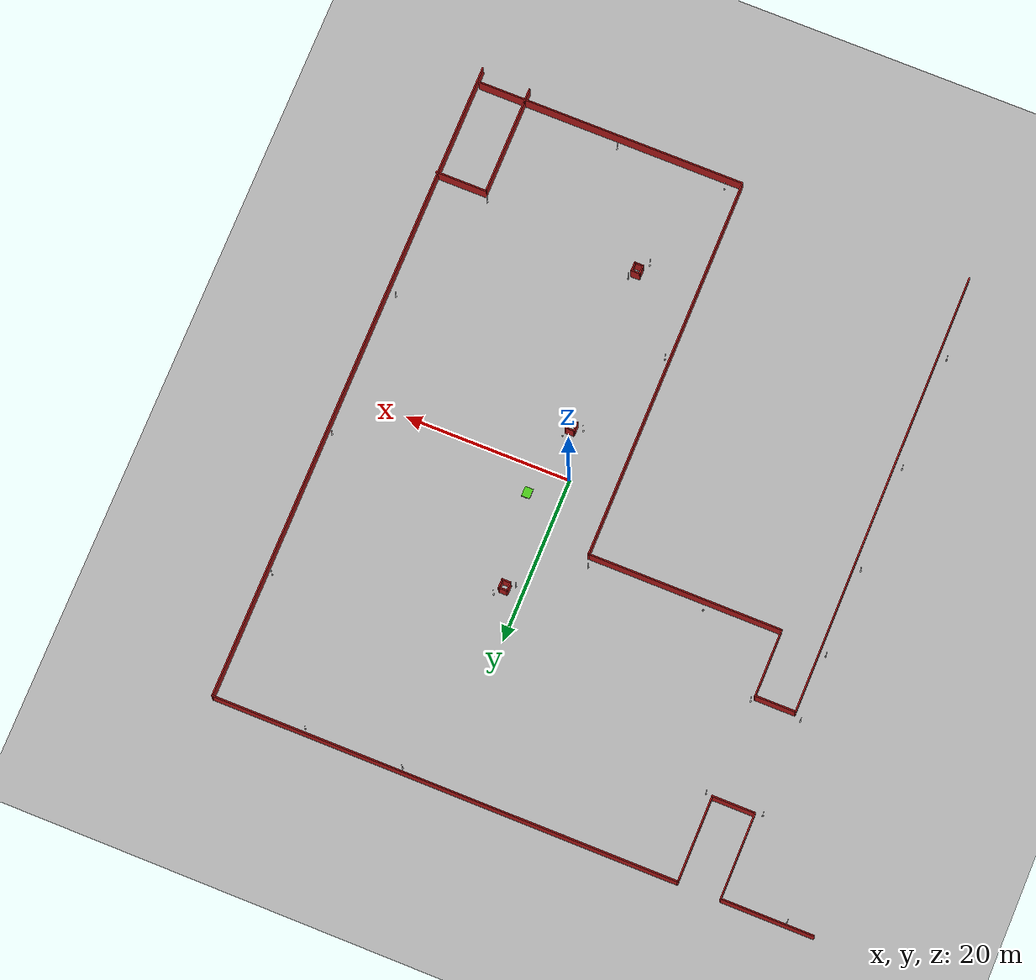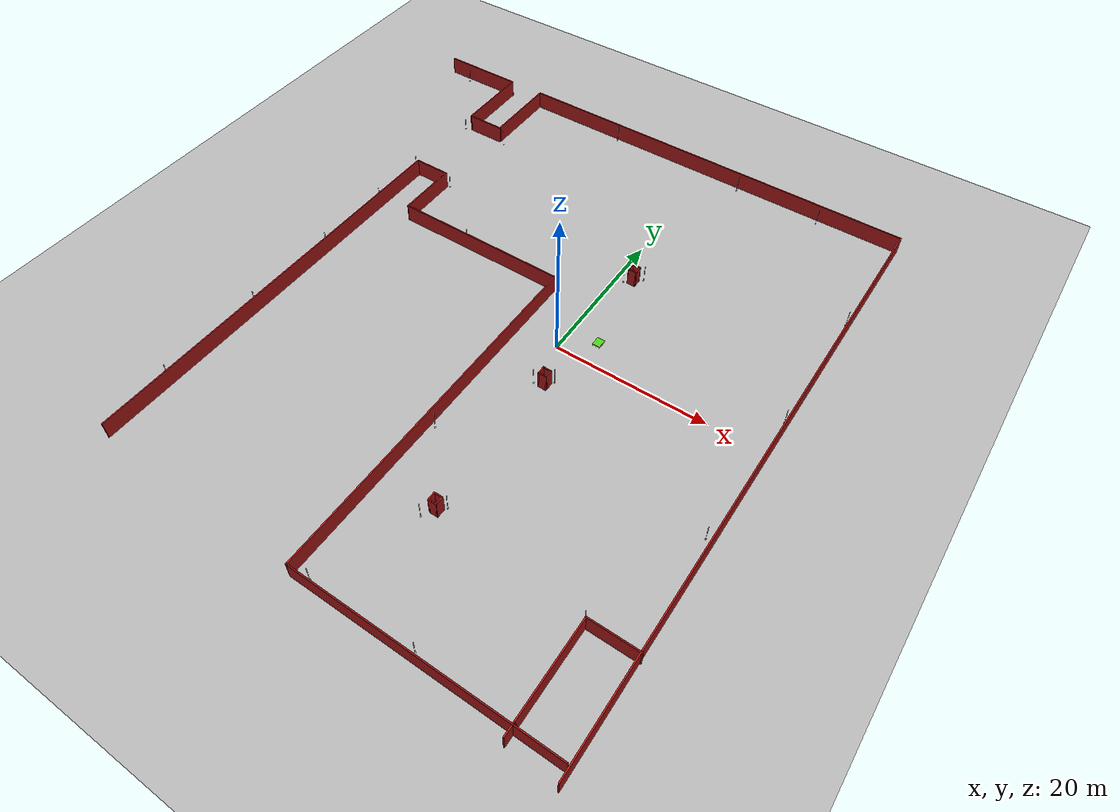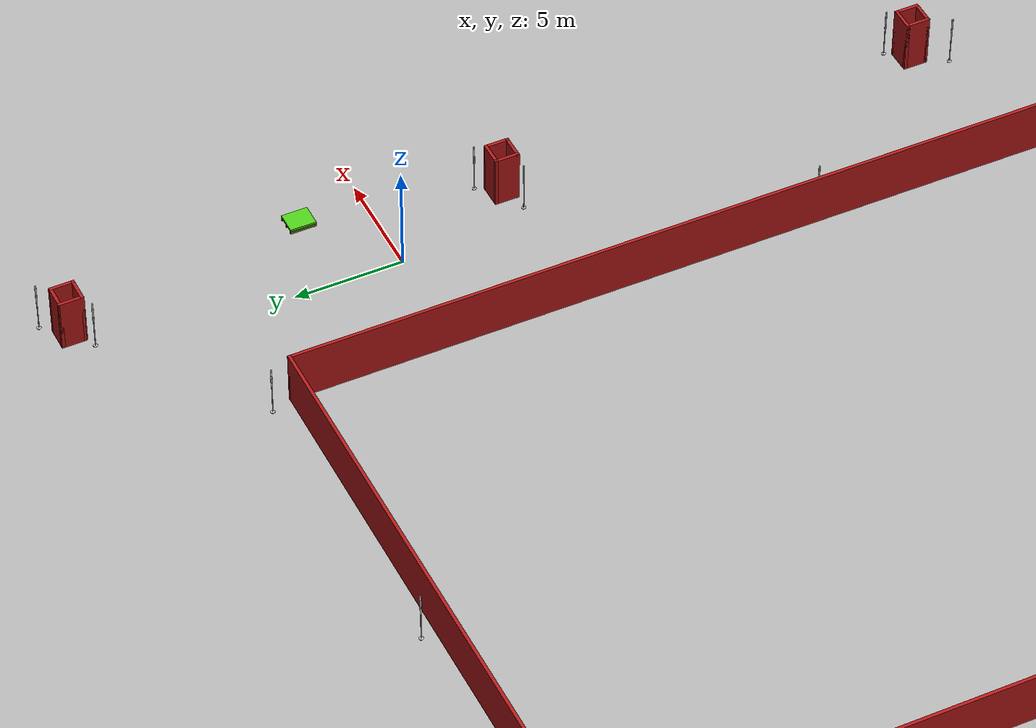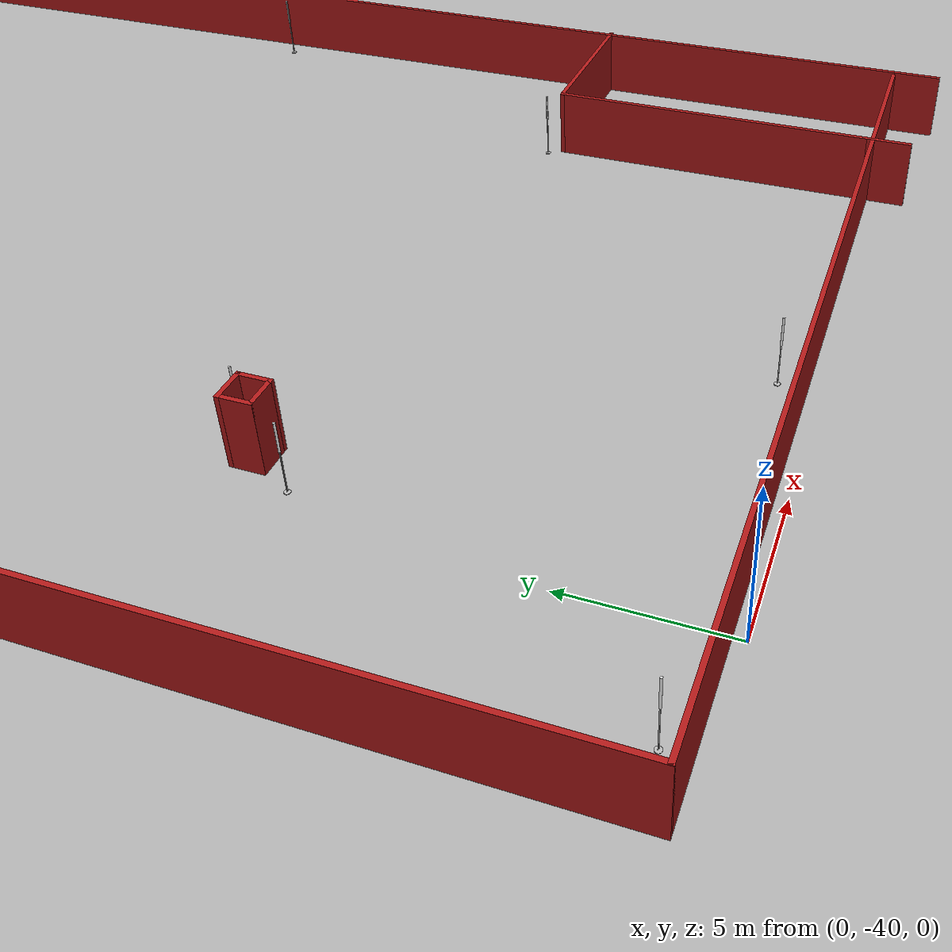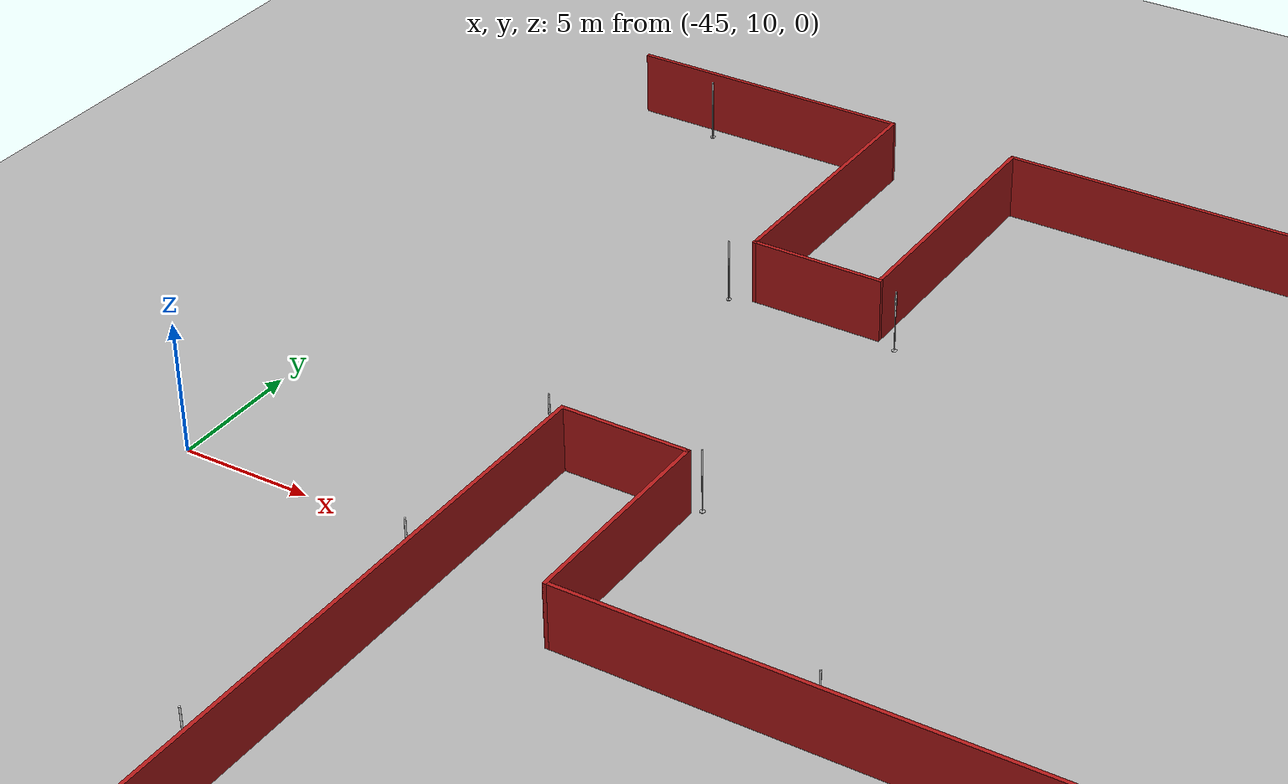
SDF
<?xml version='1.0'?>
<sdf version="1.9">
  <world name="empty">
    <physics name="default_physics" type="dart">
      <max_step_size>0.005</max_step_size>
      <real_time_factor>1.0</real_time_factor>
    </physics>

    <plugin filename="gz-sim-user-commands-system" name="gz::sim::systems::UserCommands">
    </plugin>
    <plugin filename="gz-sim-scene-broadcaster-system" name="gz::sim::systems::SceneBroadcaster">
    </plugin>
    <plugin filename="gz-sim-contact-system" name="gz::sim::systems::Contact">
    </plugin>
    <plugin filename="gz-sim-sensors-system" name="gz::sim::systems::Sensors">
      <render_engine>ogre2</render_engine>
    </plugin>
    <plugin filename="gz-sim-physics-system" name="gz::sim::systems::Physics">
      <use_attach_mesh_shape_feature>true</use_attach_mesh_shape_feature>
    </plugin>
    <plugin filename="gz-sim-imu-system" name="gz::sim::systems::Imu">
    </plugin>

    <light type="directional" name="sun">
      <cast_shadows>true</cast_shadows>
      <pose>0 0 10 0 0 0</pose>
      <diffuse>0.8 0.8 0.8 1</diffuse>
      <specular>0.2 0.2 0.2 1</specular>
      <attenuation>
        <range>1000</range>
        <constant>0.9</constant>
        <linear>0.01</linear>
        <quadratic>0.001</quadratic>
      </attenuation>
      <direction>-0.5 0.1 -0.9</direction>
    </light>

    <model name='ground_plane'>
      <static>1</static>
      <link name='link'>
        <collision name='collision'>
          <geometry>
            <plane>
              <normal>0 0 1</normal>
              <size>100 100</size>
            </plane>
          </geometry>
          <max_contacts>50</max_contacts>
          <surface>
            <friction>
              <ode>
                <mu>100</mu>
                <mu2>100</mu2>
              </ode>
            </friction>
          </surface>
        </collision>
        <visual name='visual'>
          <cast_shadows>0</cast_shadows>
          <geometry>
            <plane>
              <normal>0 0 1</normal>
              <size>100 100</size>
            </plane>
          </geometry>
          <material>
            <ambient>0.8 0.8 0.8 1</ambient>
            <diffuse>0.7 0.7 0.7 1</diffuse>
            <specular>0.8 0.8 0.8 1</specular>
          </material>
        </visual>
        <self_collide>0</self_collide>
        <kinematic>0</kinematic>
        <gravity>1</gravity>
      </link>
    </model>
    <model name="pallet">
      <pose>3.9 3.1 0.4 0 0 1.5708</pose>
      <link name="left">
        <pose relative_to="up">0 -0.45 -0.125 0 0 0</pose>
        <visual name="left_visual">
          <geometry>
            <box>
              <size>1.2 0.1 0.15</size>
            </box>
          </geometry>
          <pose>0.0 0.0 0.0 0.0 0.0 0.0 </pose>
          <material>
            <ambient>0.8 0.8 0.8 1</ambient>
            <diffuse>0.3 0.1 0.1 1</diffuse>
            <specular>0.8 0.8 0.8 1</specular>
          </material>
          <laser_retro>0</laser_retro>
        </visual>
        <collision name="left_collision">
          <geometry>
            <box>
              <size>1.2 0.1 0.15</size>
            </box>
          </geometry>
          <pose>0.0 0.0 0.0 0.0 0.0 0.0 </pose>
          <surface>
            <friction>
              <ode>
                <mu>0.05</mu>
                <mu2>0.05</mu2>
              </ode>
            </friction>
          </surface>
        </collision>
      </link>

      <link name="mid">
        <pose relative_to="up">0 0 -0.125 0 0 0</pose>
        <visual name="mid_visual">
          <geometry>
            <box >
              <size>
            1.2 0.1 0.15</size>
            </box>
          </geometry>
          <pose>0.0 0.0 0.0 0.0 0.0 0.0 </pose>
          <material>
            <ambient>0.8 0.8 0.8 1</ambient>
            <diffuse>0.3 0.1 0.1 1</diffuse>
            <specular>0.8 0.8 0.8 1</specular>
          </material>
          <laser_retro>0</laser_retro>
        </visual>
        <collision name="mid_collision">
          <geometry>
            <box >
              <size>
            1.2 0.1 0.15</size>
            </box>
          </geometry>
          <pose>0.0 0.0 0.0 0.0 0.0 0.0 </pose>
          <surface>
            <friction>
              <ode>
                <mu>0.05</mu>
                <mu2>0.05</mu2>
              </ode>
            </friction>
          </surface>
        </collision>
      </link>

      <link name="right">
        <inertial auto="true">
          <mass>5</mass>
          <density>200</density>
        </inertial>
        <visual name="right_visual">
          <geometry>
            <box>
              <size>1.2 0.1 0.15</size>
            </box>
          </geometry>
          <pose>0.0 0.0 0 0.0 0.0 0.0 </pose>
          <material>
            <ambient>0.8 0.8 0.8 1</ambient>
            <diffuse>0.3 0.4 0.1 1</diffuse>
            <specular>0.8 0.8 0.8 1</specular>
          </material>
          <laser_retro>0</laser_retro>

        </visual>
        <collision name="right_collision">
          <geometry>
            <box>
              <size>1.2 0.1 0.15</size>
            </box>
          </geometry>
          <pose>0.0 0.0 0 0.0 0.0 0.0 </pose>

          <surface>
            <friction>
              <ode>
                <mu>0.05</mu>
                <mu2>0.05</mu2>
              </ode>
            </friction>
          </surface>
        </collision>
        <pose relative_to="up">0 0.45 -0.125 0 0 0</pose>
      </link>

      <link name="up">
        <inertial auto="true">
          <mass>20</mass>
          <density>200</density>
        </inertial>
        <visual name="up_visual">
          <geometry>
            <box >
              <size>1.2 1.0 0.1</size>
            </box>
          </geometry>
          <pose>0.0 0.0 0 0.0 0.0 0.0 </pose>
          <material>
            <ambient>0.8 0.8 0.8 1</ambient>
            <diffuse>0.3 0.8 0.1 1</diffuse>
            <specular>0.8 0.8 0.8 1</specular>
          </material>
          <laser_retro>0</laser_retro>

        </visual>
        <collision name="up_collision">
          <geometry>
            <box >
              <size>1.2 1.0 0.1</size>
            </box>
          </geometry>
          <pose>0.0 0.0 0 0.0 0.0 0.0 </pose>

          <surface>
            <friction>
              <ode>
                <mu>10000.0</mu>
                <mu2>10000.0</mu2>
              </ode>
            </friction>
          </surface>

        </collision>
      </link>

      <!-- main chasis + RR wheel joining-->
      <joint name="joint0" type="fixed">
        <axis>
          <xyz>0 0 1</xyz>
        </axis>
        <parent>up</parent>
        <child>left</child>
      </joint>
      <joint name="joint1" type="fixed">
        <axis>
          <xyz>0 0 1</xyz>
        </axis>
        <parent> up </parent>
        <child> mid </child>
      </joint>
      <joint name="joint2" type="fixed">
        <axis>
          <xyz>0 0 1</xyz>
        </axis>
        <parent> up </parent>
        <child> right </child>
      </joint>
    </model>
    <model name='beijing_daxing'>
      <pose  >-8.50336 -1.45024 0 0 -0 0</pose>
      <link name='Wall_0'>
        <collision name='Wall_0_Collision'>
          <geometry>
            <box>
              <size>56.15 0.15 2.5</size>
            </box>
          </geometry>
          <pose  >0 0 1.25 0 -0 0</pose>
          <max_contacts>10</max_contacts>
          <surface>
            <contact>
              <ode/>
            </contact>
            <bounce/>
            <friction>
              <torsional>
                <ode/>
              </torsional>
              <ode/>
            </friction>
          </surface>
        </collision>
        <visual name='Wall_0_Visual'>
          <pose  >0 0 1.25 0 -0 0</pose>
          <geometry>
            <box>
              <size>56.15 0.15 2.5</size>
            </box>
          </geometry>
          <material>
            <ambient>0.8 0.8 0.8 1</ambient>
            <diffuse>0.7 0.1 0.1 1</diffuse>
            <specular>0.8 0.8 0.8 1</specular>
          </material>
          <laser_retro>0</laser_retro>

        </visual>
        <pose  >8.03453 39.8 0 0 -0 0</pose>
        <self_collide>0</self_collide>
        <kinematic>0</kinematic>
        <gravity>1</gravity>
      </link>
      <link name='Wall_10'>
        <collision name='Wall_10_Collision'>
          <geometry>
            <box>
              <size>47.25 0.15 2.5</size>
            </box>
          </geometry>
          <pose  >0 0 1.25 0 -0 0</pose>
          <max_contacts>10</max_contacts>
          <surface>
            <contact>
              <ode/>
            </contact>
            <bounce/>
            <friction>
              <torsional>
                <ode/>
              </torsional>
              <ode/>
            </friction>
          </surface>
        </collision>
        <visual name='Wall_10_Visual'>
          <pose  >0 0 1.25 0 -0 0</pose>
          <geometry>
            <box>
              <size>47.25 0.15 2.5</size>
            </box>
          </geometry>
          <material>
            <ambient>0.8 0.8 0.8 1</ambient>
            <diffuse>0.7 0.1 0.1 1</diffuse>
            <specular>0.8 0.8 0.8 1</specular>
          </material>
          <laser_retro>0</laser_retro>
        </visual>
        <pose  >3.13453 -14.55 0 0 0 -1.5708</pose>
        <self_collide>0</self_collide>
        <kinematic>0</kinematic>
        <gravity>1</gravity>
      </link>
      <link name='Wall_101'>
        <collision name='Wall_101_Collision'>
          <geometry>
            <box>
              <size>6.25 0.15 2.5</size>
            </box>
          </geometry>
          <pose  >0 0 1.25 0 -0 0</pose>
          <max_contacts>10</max_contacts>
          <surface>
            <contact>
              <ode/>
            </contact>
            <bounce/>
            <friction>
              <torsional>
                <ode/>
              </torsional>
              <ode/>
            </friction>
          </surface>
        </collision>
        <visual name='Wall_101_Visual'>
          <pose  >0 0 1.25 0 -0 0</pose>
          <geometry>
            <box>
              <size>6.25 0.15 2.5</size>
            </box>
          </geometry>
          <material>
            <ambient>0.8 0.8 0.8 1</ambient>
            <diffuse>0.7 0.1 0.1 1</diffuse>
            <specular>0.8 0.8 0.8 1</specular>
          </material>
        </visual>
        <pose  >33.1155 -26.2191 0 0 -0 3.14159</pose>
        <self_collide>0</self_collide>
        <kinematic>0</kinematic>
        <gravity>1</gravity>
      </link>
      <link name='Wall_102'>
        <collision name='Wall_102_Collision'>
          <geometry>
            <box>
              <size>11.75 0.15 2.5</size>
            </box>
          </geometry>
          <pose  >0 0 1.25 0 -0 0</pose>
          <max_contacts>10</max_contacts>
          <surface>
            <contact>
              <ode/>
            </contact>
            <bounce/>
            <friction>
              <torsional>
                <ode/>
              </torsional>
              <ode/>
            </friction>
          </surface>
        </collision>
        <visual name='Wall_102_Visual'>
          <pose  >0 0 1.25 0 -0 0</pose>
          <geometry>
            <box>
              <size>11.75 0.15 2.5</size>
            </box>
          </geometry>
          <material>
            <ambient>0.8 0.8 0.8 1</ambient>
            <diffuse>0.7 0.1 0.1 1</diffuse>
            <specular>0.8 0.8 0.8 1</specular>
          </material>
        </visual>
        <pose  >30.0655 -32.0191 0 0 0 -1.5708</pose>
        <self_collide>0</self_collide>
        <kinematic>0</kinematic>
        <gravity>1</gravity>
      </link>
      <link name='Wall_103'>
        <collision name='Wall_103_Collision'>
          <geometry>
            <box>
              <size>1.75 0.15 2.5</size>
            </box>
          </geometry>
          <pose  >0 0 1.25 0 -0 0</pose>
          <max_contacts>10</max_contacts>
          <surface>
            <contact>
              <ode/>
            </contact>
            <bounce/>
            <friction>
              <torsional>
                <ode/>
              </torsional>
              <ode/>
            </friction>
          </surface>
        </collision>
        <visual name='Wall_103_Visual'>
          <pose  >0 0 1.25 0 -0 0</pose>
          <geometry>
            <box>
              <size>1.75 0.15 2.5</size>
            </box>
          </geometry>
          <material>
            <ambient>0.8 0.8 0.8 1</ambient>
            <diffuse>0.7 0.1 0.1 1</diffuse>
            <specular>0.8 0.8 0.8 1</specular>
          </material>
        </visual>
        <pose  >30.0655 -38.6191 0 0 0 -1.5708</pose>
        <self_collide>0</self_collide>
        <kinematic>0</kinematic>
        <gravity>1</gravity>
      </link>
      <link name='Wall_105'>
        <collision name='Wall_105_Collision'>
          <geometry>
            <box>
              <size>54.5 0.15 2.5</size>
            </box>
          </geometry>
          <pose  >0 0 1.25 0 -0 0</pose>
          <max_contacts>10</max_contacts>
          <surface>
            <contact>
              <ode/>
            </contact>
            <bounce/>
            <friction>
              <torsional>
                <ode/>
              </torsional>
              <ode/>
            </friction>
          </surface>
        </collision>
        <visual name='Wall_105_Visual'>
          <pose  >0 0 1.25 0 -0 0</pose>
          <geometry>
            <box>
              <size>54.5 0.15 2.5</size>
            </box>
          </geometry>
          <material>
            <ambient>0.8 0.8 0.8 1</ambient>
            <diffuse>0.7 0.1 0.1 1</diffuse>
            <specular>0.8 0.8 0.8 1</specular>
          </material>
        </visual>
        <pose  >-25.0655 -10.075 0 0 0 -1.5708</pose>
        <self_collide>0</self_collide>
        <kinematic>0</kinematic>
        <gravity>1</gravity>
      </link>
      <link name='Wall_11'>
        <collision name='Wall_11_Collision'>
          <geometry>
            <box>
              <size>32.75 0.15 2.5</size>
            </box>
          </geometry>
          <pose  >0 0 1.25 0 -0 0</pose>
          <max_contacts>10</max_contacts>
          <surface>
            <contact>
              <ode/>
            </contact>
            <bounce/>
            <friction>
              <torsional>
                <ode/>
              </torsional>
              <ode/>
            </friction>
          </surface>
        </collision>
        <visual name='Wall_11_Visual'>
          <pose  >0 0 1.25 0 -0 0</pose>
          <geometry>
            <box>
              <size>32.75 0.15 2.5</size>
            </box>
          </geometry>
          <material>
            <ambient>0.8 0.8 0.8 1</ambient>
            <diffuse>0.7 0.1 0.1 1</diffuse>
            <specular>0.8 0.8 0.8 1</specular>
          </material>
        </visual>
        <pose  >19.4345 -38.1 0 0 -0 0</pose>
        <self_collide>0</self_collide>
        <kinematic>0</kinematic>
        <gravity>1</gravity>
      </link>
      <link name='Wall_13'>
        <collision name='Wall_13_Collision'>
          <geometry>
            <box>
              <size>10.5 0.15 2.5</size>
            </box>
          </geometry>
          <pose  >0 0 1.25 0 -0 0</pose>
          <max_contacts>10</max_contacts>
          <surface>
            <contact>
              <ode/>
            </contact>
            <bounce/>
            <friction>
              <torsional>
                <ode/>
              </torsional>
              <ode/>
            </friction>
          </surface>
        </collision>
        <visual name='Wall_13_Visual'>
          <pose  >0 0 1.25 0 -0 0</pose>
          <geometry>
            <box>
              <size>10.5 0.15 2.5</size>
            </box>
          </geometry>
          <material>
            <ambient>0.8 0.8 0.8 1</ambient>
            <diffuse>0.7 0.1 0.1 1</diffuse>
            <specular>0.8 0.8 0.8 1</specular>
          </material>
        </visual>
        <pose  >-25.0655 34.625 0 0 -0 1.5708</pose>
        <self_collide>0</self_collide>
        <kinematic>0</kinematic>
        <gravity>1</gravity>
      </link>
      <link name='Wall_14'>
        <collision name='Wall_14_Collision'>
          <geometry>
            <box>
              <size>11.25 0.15 2.5</size>
            </box>
          </geometry>
          <pose  >0 0 1.25 0 -0 0</pose>
          <max_contacts>10</max_contacts>
          <surface>
            <contact>
              <ode/>
            </contact>
            <bounce/>
            <friction>
              <torsional>
                <ode/>
              </torsional>
              <ode/>
            </friction>
          </surface>
        </collision>
        <visual name='Wall_14_Visual'>
          <pose  >0 0 1.25 0 -0 0</pose>
          <geometry>
            <box>
              <size>11.25 0.15 2.5</size>
            </box>
          </geometry>
          <material>
            <ambient>0.8 0.8 0.8 1</ambient>
            <diffuse>0.7 0.1 0.1 1</diffuse>
            <specular>0.8 0.8 0.8 1</specular>
          </material>
        </visual>
        <pose  >-30.6155 39.8 0 0 -0 3.14159</pose>
        <self_collide>0</self_collide>
        <kinematic>0</kinematic>
        <gravity>1</gravity>
      </link>
      <link name='Wall_2'>
        <collision name='Wall_2_Collision'>
          <geometry>
            <box>
              <size>79.75 0.15 2.5</size>
            </box>
          </geometry>
          <pose  >0 0 1.25 0 -0 0</pose>
          <max_contacts>10</max_contacts>
          <surface>
            <contact>
              <ode/>
            </contact>
            <bounce/>
            <friction>
              <torsional>
                <ode/>
              </torsional>
              <ode/>
            </friction>
          </surface>
        </collision>
        <visual name='Wall_2_Visual'>
          <pose  >0 0 1.25 0 -0 0</pose>
          <geometry>
            <box>
              <size>79.75 0.15 2.5</size>
            </box>
          </geometry>
          <material>
            <ambient>0.8 0.8 0.8 1</ambient>
            <diffuse>0.7 0.1 0.1 1</diffuse>
            <specular>0.8 0.8 0.8 1</specular>
          </material>
        </visual>
        <pose  >36.0345 0 0 0 0 -1.5708</pose>
        <self_collide>0</self_collide>
        <kinematic>0</kinematic>
        <gravity>1</gravity>
      </link>
      <link name='Wall_4'>
        <collision name='Wall_4_Collision'>
          <geometry>
            <box>
              <size>10.5 0.15 2.5</size>
            </box>
          </geometry>
          <pose  >0 0 1.25 0 -0 0</pose>
          <max_contacts>10</max_contacts>
          <surface>
            <contact>
              <ode/>
            </contact>
            <bounce/>
            <friction>
              <torsional>
                <ode/>
              </torsional>
              <ode/>
            </friction>
          </surface>
        </collision>
        <visual name='Wall_4_Visual'>
          <pose  >0 0 1.25 0 -0 0</pose>
          <geometry>
            <box>
              <size>10.5 0.15 2.5</size>
            </box>
          </geometry>
          <material>
            <ambient>0.8 0.8 0.8 1</ambient>
            <diffuse>0.7 0.1 0.1 1</diffuse>
            <specular>0.8 0.8 0.8 1</specular>
          </material>
        </visual>
        <pose  >-19.9655 34.625 0 0 0 -1.5708</pose>
        <self_collide>0</self_collide>
        <kinematic>0</kinematic>
        <gravity>1</gravity>
      </link>
      <link name='Wall_5'>
        <collision name='Wall_5_Collision'>
          <geometry>
            <box>
              <size>5.25 0.15 2.5</size>
            </box>
          </geometry>
          <pose  >0 0 1.25 0 -0 0</pose>
          <max_contacts>10</max_contacts>
          <surface>
            <contact>
              <ode/>
            </contact>
            <bounce/>
            <friction>
              <torsional>
                <ode/>
              </torsional>
              <ode/>
            </friction>
          </surface>
        </collision>
        <visual name='Wall_5_Visual'>
          <pose  >0 0 1.25 0 -0 0</pose>
          <geometry>
            <box>
              <size>5.25 0.15 2.5</size>
            </box>
          </geometry>
          <material>
            <ambient>0.8 0.8 0.8 1</ambient>
            <diffuse>0.7 0.1 0.1 1</diffuse>
            <specular>0.8 0.8 0.8 1</specular>
          </material>
        </visual>
        <pose  >-22.5155 29.45 0 0 -0 3.14159</pose>
        <self_collide>0</self_collide>
        <kinematic>0</kinematic>
        <gravity>1</gravity>
      </link>
      <link name='Wall_7'>
        <collision name='Wall_7_Collision'>
          <geometry>
            <box>
              <size>5 0.15 2.5</size>
            </box>
          </geometry>
          <pose  >0 0 1.25 0 -0 0</pose>
          <max_contacts>10</max_contacts>
          <surface>
            <contact>
              <ode/>
            </contact>
            <bounce/>
            <friction>
              <torsional>
                <ode/>
              </torsional>
              <ode/>
            </friction>
          </surface>
        </collision>
        <visual name='Wall_7_Visual'>
          <pose  >0 0 1.25 0 -0 0</pose>
          <geometry>
            <box>
              <size>5 0.15 2.5</size>
            </box>
          </geometry>
          <material>
            <ambient>0.8 0.8 0.8 1</ambient>
            <diffuse>0.7 0.1 0.1 1</diffuse>
            <specular>0.8 0.8 0.8 1</specular>
          </material>
        </visual>
        <pose  >-22.6405 17.1 0 0 -0 0</pose>
        <self_collide>0</self_collide>
        <kinematic>0</kinematic>
        <gravity>1</gravity>
      </link>
      <link name='Wall_76'>
        <collision name='Wall_76_Collision'>
          <geometry>
            <box>
              <size>1.15 0.15 2.5</size>
            </box>
          </geometry>
          <pose  >0 0 1.25 0 -0 0</pose>
          <max_contacts>10</max_contacts>
          <surface>
            <contact>
              <ode/>
            </contact>
            <bounce/>
            <friction>
              <torsional>
                <ode/>
              </torsional>
              <ode/>
            </friction>
          </surface>
        </collision>
        <visual name='Wall_76_Visual'>
          <pose  >0 0 1.25 0 -0 0</pose>
          <geometry>
            <box>
              <size>1.15 0.15 2.5</size>
            </box>
          </geometry>
          <material>
            <ambient>0.8 0.8 0.8 1</ambient>
            <diffuse>0.7 0.1 0.1 1</diffuse>
            <specular>0.8 0.8 0.8 1</specular>
          </material>
        </visual>
        <pose  >10.5345 15.34 0 0 -0 0</pose>
        <self_collide>0</self_collide>
        <kinematic>0</kinematic>
        <gravity>1</gravity>
      </link>
      <link name='Wall_78'>
        <collision name='Wall_78_Collision'>
          <geometry>
            <box>
              <size>1.15 0.15 2.5</size>
            </box>
          </geometry>
          <pose  >0 0 1.25 0 -0 0</pose>
          <max_contacts>10</max_contacts>
          <surface>
            <contact>
              <ode/>
            </contact>
            <bounce/>
            <friction>
              <torsional>
                <ode/>
              </torsional>
              <ode/>
            </friction>
          </surface>
        </collision>
        <visual name='Wall_78_Visual'>
          <pose  >0 0 1.25 0 -0 0</pose>
          <geometry>
            <box>
              <size>1.15 0.15 2.5</size>
            </box>
          </geometry>
          <material>
            <ambient>0.8 0.8 0.8 1</ambient>
            <diffuse>0.7 0.1 0.1 1</diffuse>
            <specular>0.8 0.8 0.8 1</specular>
          </material>
        </visual>
        <pose  >10.5345 16.34 0 0 -0 0</pose>
        <self_collide>0</self_collide>
        <kinematic>0</kinematic>
        <gravity>1</gravity>
      </link>
      <link name='Wall_8'>
        <collision name='Wall_8_Collision'>
          <geometry>
            <box>
              <size>8.25 0.15 2.5</size>
            </box>
          </geometry>
          <pose  >0 0 1.25 0 -0 0</pose>
          <max_contacts>10</max_contacts>
          <surface>
            <contact>
              <ode/>
            </contact>
            <bounce/>
            <friction>
              <torsional>
                <ode/>
              </torsional>
              <ode/>
            </friction>
          </surface>
        </collision>
        <visual name='Wall_8_Visual'>
          <pose  >0 0 1.25 0 -0 0</pose>
          <geometry>
            <box>
              <size>8.25 0.15 2.5</size>
            </box>
          </geometry>
          <material>
            <ambient>0.8 0.8 0.8 1</ambient>
            <diffuse>0.7 0.1 0.1 1</diffuse>
            <specular>0.8 0.8 0.8 1</specular>
          </material>
        </visual>
        <pose  >-20.2155 13.05 0 0 0 -1.5708</pose>
        <self_collide>0</self_collide>
        <kinematic>0</kinematic>
        <gravity>1</gravity>
      </link>
      <link name='Wall_81'>
        <collision name='Wall_81_Collision'>
          <geometry>
            <box>
              <size>1.15 0.15 2.5</size>
            </box>
          </geometry>
          <pose  >0 0 1.25 0 -0 0</pose>
          <max_contacts>10</max_contacts>
          <surface>
            <contact>
              <ode/>
            </contact>
            <bounce/>
            <friction>
              <torsional>
                <ode/>
              </torsional>
              <ode/>
            </friction>
          </surface>
        </collision>
        <visual name='Wall_81_Visual'>
          <pose  >0 0 1.25 0 -0 0</pose>
          <geometry>
            <box>
              <size>1.15 0.15 2.5</size>
            </box>
          </geometry>
          <material>
            <ambient>0.8 0.8 0.8 1</ambient>
            <diffuse>0.7 0.1 0.1 1</diffuse>
            <specular>0.8 0.8 0.8 1</specular>
          </material>
        </visual>
        <pose  >10.0345 15.84 0 0 0 -1.5708</pose>
        <self_collide>0</self_collide>
        <kinematic>0</kinematic>
        <gravity>1</gravity>
      </link>
      <link name='Wall_83'>
        <collision name='Wall_83_Collision'>
          <geometry>
            <box>
              <size>1.15 0.15 2.5</size>
            </box>
          </geometry>
          <pose  >0 0 1.25 0 -0 0</pose>
          <max_contacts>10</max_contacts>
          <surface>
            <contact>
              <ode/>
            </contact>
            <bounce/>
            <friction>
              <torsional>
                <ode/>
              </torsional>
              <ode/>
            </friction>
          </surface>
        </collision>
        <visual name='Wall_83_Visual'>
          <pose  >0 0 1.25 0 -0 0</pose>
          <geometry>
            <box>
              <size>1.15 0.15 2.5</size>
            </box>
          </geometry>
          <material>
            <ambient>0.8 0.8 0.8 1</ambient>
            <diffuse>0.7 0.1 0.1 1</diffuse>
            <specular>0.8 0.8 0.8 1</specular>
          </material>
        </visual>
        <pose  >11.0345 15.84 0 0 0 -1.5708</pose>
        <self_collide>0</self_collide>
        <kinematic>0</kinematic>
        <gravity>1</gravity>
      </link>
      <link name='Wall_85'>
        <collision name='Wall_85_Collision'>
          <geometry>
            <box>
              <size>1.15 0.15 2.5</size>
            </box>
          </geometry>
          <pose  >0 0 1.25 0 -0 0</pose>
          <max_contacts>10</max_contacts>
          <surface>
            <contact>
              <ode/>
            </contact>
            <bounce/>
            <friction>
              <torsional>
                <ode/>
              </torsional>
              <ode/>
            </friction>
          </surface>
        </collision>
        <visual name='Wall_85_Visual'>
          <pose  >0 0 1.25 0 -0 0</pose>
          <geometry>
            <box>
              <size>1.15 0.15 2.5</size>
            </box>
          </geometry>
          <material>
            <ambient>0.8 0.8 0.8 1</ambient>
            <diffuse>0.7 0.1 0.1 1</diffuse>
            <specular>0.8 0.8 0.8 1</specular>
          </material>
        </visual>
        <pose  >10.5345 -3.66 0 0 -0 0</pose>
        <self_collide>0</self_collide>
        <kinematic>0</kinematic>
        <gravity>1</gravity>
      </link>
      <link name='Wall_87'>
        <collision name='Wall_87_Collision'>
          <geometry>
            <box>
              <size>1.15 0.15 2.5</size>
            </box>
          </geometry>
          <pose  >0 0 1.25 0 -0 0</pose>
          <max_contacts>10</max_contacts>
          <surface>
            <contact>
              <ode/>
            </contact>
            <bounce/>
            <friction>
              <torsional>
                <ode/>
              </torsional>
              <ode/>
            </friction>
          </surface>
        </collision>
        <visual name='Wall_87_Visual'>
          <pose  >0 0 1.25 0 -0 0</pose>
          <geometry>
            <box>
              <size>1.15 0.15 2.5</size>
            </box>
          </geometry>
          <material>
            <ambient>0.8 0.8 0.8 1</ambient>
            <diffuse>0.7 0.1 0.1 1</diffuse>
            <specular>0.8 0.8 0.8 1</specular>
          </material>
        </visual>
        <pose  >10.5345 -4.66 0 0 -0 0</pose>
        <self_collide>0</self_collide>
        <kinematic>0</kinematic>
        <gravity>1</gravity>
      </link>
      <link name='Wall_89'>
        <collision name='Wall_89_Collision'>
          <geometry>
            <box>
              <size>1.15 0.15 2.5</size>
            </box>
          </geometry>
          <pose  >0 0 1.25 0 -0 0</pose>
          <max_contacts>10</max_contacts>
          <surface>
            <contact>
              <ode/>
            </contact>
            <bounce/>
            <friction>
              <torsional>
                <ode/>
              </torsional>
              <ode/>
            </friction>
          </surface>
        </collision>
        <visual name='Wall_89_Visual'>
          <pose  >0 0 1.25 0 -0 0</pose>
          <geometry>
            <box>
              <size>1.15 0.15 2.5</size>
            </box>
          </geometry>
          <material>
            <ambient>0.8 0.8 0.8 1</ambient>
            <diffuse>0.7 0.1 0.1 1</diffuse>
            <specular>0.8 0.8 0.8 1</specular>
          </material>
        </visual>
        <pose  >10.0345 -4.16 0 0 0 -1.5708</pose>
        <self_collide>0</self_collide>
        <kinematic>0</kinematic>
        <gravity>1</gravity>
      </link>
      <link name='Wall_9'>
        <collision name='Wall_9_Collision'>
          <geometry>
            <box>
              <size>23.5 0.15 2.5</size>
            </box>
          </geometry>
          <pose  >0 0 1.25 0 -0 0</pose>
          <max_contacts>10</max_contacts>
          <surface>
            <contact>
              <ode/>
            </contact>
            <bounce/>
            <friction>
              <torsional>
                <ode/>
              </torsional>
              <ode/>
            </friction>
          </surface>
        </collision>
        <visual name='Wall_9_Visual'>
          <pose  >0 0 1.25 0 -0 0</pose>
          <geometry>
            <box>
              <size>23.5 0.15 2.5</size>
            </box>
          </geometry>
          <material>
            <ambient>0.8 0.8 0.8 1</ambient>
            <diffuse>0.7 0.1 0.1 1</diffuse>
            <specular>0.8 0.8 0.8 1</specular>
          </material>
        </visual>
        <pose  >-8.54047 9 0 0 -0 0</pose>
        <self_collide>0</self_collide>
        <kinematic>0</kinematic>
        <gravity>1</gravity>
      </link>
      <link name='Wall_91'>
        <collision name='Wall_91_Collision'>
          <geometry>
            <box>
              <size>1.15 0.15 2.5</size>
            </box>
          </geometry>
          <pose  >0 0 1.25 0 -0 0</pose>
          <max_contacts>10</max_contacts>
          <surface>
            <contact>
              <ode/>
            </contact>
            <bounce/>
            <friction>
              <torsional>
                <ode/>
              </torsional>
              <ode/>
            </friction>
          </surface>
        </collision>
        <visual name='Wall_91_Visual'>
          <pose  >0 0 1.25 0 -0 0</pose>
          <geometry>
            <box>
              <size>1.15 0.15 2.5</size>
            </box>
          </geometry>
          <material>
            <ambient>0.8 0.8 0.8 1</ambient>
            <diffuse>0.7 0.1 0.1 1</diffuse>
            <specular>0.8 0.8 0.8 1</specular>
          </material>
        </visual>
        <pose  >11.0345 -4.16 0 0 0 -1.5708</pose>
        <self_collide>0</self_collide>
        <kinematic>0</kinematic>
        <gravity>1</gravity>
      </link>
      <link name='Wall_93'>
        <collision name='Wall_93_Collision'>
          <geometry>
            <box>
              <size>1.15 0.15 2.5</size>
            </box>
          </geometry>
          <pose  >0 0 1.25 0 -0 0</pose>
          <max_contacts>10</max_contacts>
          <surface>
            <contact>
              <ode/>
            </contact>
            <bounce/>
            <friction>
              <torsional>
                <ode/>
              </torsional>
              <ode/>
            </friction>
          </surface>
        </collision>
        <visual name='Wall_93_Visual'>
          <pose  >0 0 1.25 0 -0 0</pose>
          <geometry>
            <box>
              <size>1.15 0.15 2.5</size>
            </box>
          </geometry>
          <material>
            <ambient>0.8 0.8 0.8 1</ambient>
            <diffuse>0.7 0.1 0.1 1</diffuse>
            <specular>0.8 0.8 0.8 1</specular>
          </material>
        </visual>
        <pose  >10.5345 -23.66 0 0 -0 0</pose>
        <self_collide>0</self_collide>
        <kinematic>0</kinematic>
        <gravity>1</gravity>
      </link>
      <link name='Wall_95'>
        <collision name='Wall_95_Collision'>
          <geometry>
            <box>
              <size>1.15 0.15 2.5</size>
            </box>
          </geometry>
          <pose  >0 0 1.25 0 -0 0</pose>
          <max_contacts>10</max_contacts>
          <surface>
            <contact>
              <ode/>
            </contact>
            <bounce/>
            <friction>
              <torsional>
                <ode/>
              </torsional>
              <ode/>
            </friction>
          </surface>
        </collision>
        <visual name='Wall_95_Visual'>
          <pose  >0 0 1.25 0 -0 0</pose>
          <geometry>
            <box>
              <size>1.15 0.15 2.5</size>
            </box>
          </geometry>
          <material>
            <ambient>0.8 0.8 0.8 1</ambient>
            <diffuse>0.7 0.1 0.1 1</diffuse>
            <specular>0.8 0.8 0.8 1</specular>
          </material>
        </visual>
        <pose  >10.5345 -24.66 0 0 -0 0</pose>
        <self_collide>0</self_collide>
        <kinematic>0</kinematic>
        <gravity>1</gravity>
      </link>
      <link name='Wall_97'>
        <collision name='Wall_97_Collision'>
          <geometry>
            <box>
              <size>1.15 0.15 2.5</size>
            </box>
          </geometry>
          <pose  >0 0 1.25 0 -0 0</pose>
          <max_contacts>10</max_contacts>
          <surface>
            <contact>
              <ode/>
            </contact>
            <bounce/>
            <friction>
              <torsional>
                <ode/>
              </torsional>
              <ode/>
            </friction>
          </surface>
        </collision>
        <visual name='Wall_97_Visual'>
          <pose  >0 0 1.25 0 -0 0</pose>
          <geometry>
            <box>
              <size>1.15 0.15 2.5</size>
            </box>
          </geometry>
          <material>
            <ambient>0.8 0.8 0.8 1</ambient>
            <diffuse>0.7 0.1 0.1 1</diffuse>
            <specular>0.8 0.8 0.8 1</specular>
          </material>
        </visual>
        <pose  >10.0345 -24.16 0 0 0 -1.5708</pose>
        <self_collide>0</self_collide>
        <kinematic>0</kinematic>
        <gravity>1</gravity>
      </link>
      <link name='Wall_99'>
        <collision name='Wall_99_Collision'>
          <geometry>
            <box>
              <size>1.15 0.15 2.5</size>
            </box>
          </geometry>
          <pose  >0 0 1.25 0 -0 0</pose>
          <max_contacts>10</max_contacts>
          <surface>
            <contact>
              <ode/>
            </contact>
            <bounce/>
            <friction>
              <torsional>
                <ode/>
              </torsional>
              <ode/>
            </friction>
          </surface>
        </collision>
        <visual name='Wall_99_Visual'>
          <pose  >0 0 1.25 0 -0 0</pose>
          <geometry>
            <box>
              <size>1.15 0.15 2.5</size>
            </box>
          </geometry>
          <material>
            <ambient>0.8 0.8 0.8 1</ambient>
            <diffuse>0.7 0.1 0.1 1</diffuse>
            <specular>0.8 0.8 0.8 1</specular>
          </material>
        </visual>
        <pose  >11.0345 -24.16 0 0 0 -1.5708</pose>
        <self_collide>0</self_collide>
        <kinematic>0</kinematic>
        <gravity>1</gravity>
      </link>
      <static>1</static>
    </model>
    <model name='reflect_pillar_0'>
      <link name='link_dizuo'>
        <pose  >0 0 0.02 0 -0 0</pose>
        <inertial>
          <mass>20.39</mass>
          <inertia>
            <ixx>0.10058</ixx>
            <ixy>0</ixy>
            <ixz>0</ixz>
            <iyy>0.10058</iyy>
            <iyz>0</iyz>
            <izz>0.100019</izz>
          </inertia>
        </inertial>
        <collision name='collision'>
          <geometry>
            <cylinder>
              <radius>0.1</radius>
              <length>0.02</length>
            </cylinder>
          </geometry>
          <max_contacts>10</max_contacts>
          <surface>
            <contact>
              <ode/>
            </contact>
            <bounce/>
            <friction>
              <torsional>
                <ode/>
              </torsional>
              <ode/>
            </friction>
          </surface>
        </collision>
        <visual name='visual'>
          <geometry>
            <cylinder>
              <radius>0.1</radius>
              <length>0.02</length>
            </cylinder>
          </geometry>
        </visual>
        <self_collide>0</self_collide>
        <kinematic>0</kinematic>
        <gravity>1</gravity>
      </link>
      <link name='link_ganzi'>
        <pose  >0 0  0.956 0 -0 0</pose>
        <inertial>
          <mass>2.39</mass>
          <inertia>
            <ixx>0.00058</ixx>
            <ixy>0</ixy>
            <ixz>0</ixz>
            <iyy>0.00058</iyy>
            <iyz>0</iyz>
            <izz>0.00019</izz>
          </inertia>
        </inertial>
        <collision name='collision'>
          <geometry>
            <box>
              <size>0.03 0.03 1.8312</size>
            </box>
          </geometry>
          <max_contacts>10</max_contacts>
          <surface>
            <contact>
              <ode/>
            </contact>
            <bounce/>
            <friction>
              <torsional>
                <ode/>
              </torsional>
              <ode/>
            </friction>
          </surface>
        </collision>
        <visual name='visual'>
          <geometry>
            <box>
              <size>0.03 0.03 1.8312</size>
            </box>
          </geometry>
          <material>
            <ambient>0.8 0.8 0.8 1</ambient>
            <diffuse>0.7 0.1 0.1 1</diffuse>
            <specular>0.8 0.8 0.8 1</specular>
          </material>
        </visual>
        <self_collide>0</self_collide>
        <kinematic>0</kinematic>
        <gravity>1</gravity>
      </link>
      <link name='mark_1'>
        <pose  >0 0  1.9641 0 -0 0</pose>
        <inertial>
          <mass>0.39</mass>
          <inertia>
            <ixx>0.00058</ixx>
            <ixy>0</ixy>
            <ixz>0</ixz>
            <iyy>0.00058</iyy>
            <iyz>0</iyz>
            <izz>0.00019</izz>
          </inertia>
        </inertial>
        <collision name='collision'>
          <geometry>
            <cylinder>
              <radius>0.035</radius>
              <length>1</length>
            </cylinder>
          </geometry>

          <max_contacts>10</max_contacts>
          <surface>
            <contact>
              <ode/>
            </contact>
            <bounce/>
            <friction>
              <torsional>
                <ode/>
              </torsional>
              <ode/>
            </friction>
          </surface>
        </collision>
        <visual name='visual'>
          <laser_retro>  0.93</laser_retro>
          <geometry>
            <cylinder>
              <radius>0.035</radius>
              <length>1</length>
            </cylinder>
          </geometry>
          <material>
            <ambient>1 1 1 1</ambient>
            <diffuse>1 1 1 1</diffuse>
            <specular>0.99 0.99 0.99 0.99</specular>

          </material>
          <laser_retro>  0.93</laser_retro>

        </visual>
        <self_collide>0</self_collide>
        <kinematic>0</kinematic>
        <gravity>1</gravity>
      </link>
      <joint name='dizuo_ganzi_joint' type='fixed'>
        <child>link_ganzi</child>
        <parent>link_dizuo</parent>
        <axis>
          <xyz>0 0 -2</xyz>
          <limit>
            <upper>0</upper>
            <lower>0</lower>
          </limit>

        </axis>
      </joint>
      <joint name='ganzi_mark_joint' type='fixed'>
        <child>mark_1</child>
        <parent>link_ganzi</parent>
        <axis>
          <xyz>0 0 -2</xyz>
          <limit>
            <upper>0</upper>
            <lower>0</lower>
          </limit>

        </axis>
      </joint>
      <pose  >27.0809 5.02901 0 0 -0 0</pose>
    </model>
    <model name='reflect_pillar_1'>
      <link name='link_dizuo'>
        <pose  >0 0 0.02 0 -0 0</pose>
        <inertial>
          <mass>20.39</mass>
          <inertia>
            <ixx>0.10058</ixx>
            <ixy>0</ixy>
            <ixz>0</ixz>
            <iyy>0.10058</iyy>
            <iyz>0</iyz>
            <izz>0.100019</izz>
          </inertia>
        </inertial>
        <collision name='collision'>
          <geometry>
            <cylinder>
              <radius>0.1</radius>
              <length>0.02</length>
            </cylinder>
          </geometry>
          <max_contacts>10</max_contacts>
          <surface>
            <contact>
              <ode/>
            </contact>
            <bounce/>
            <friction>
              <torsional>
                <ode/>
              </torsional>
              <ode/>
            </friction>
          </surface>
        </collision>
        <visual name='visual'>
          <geometry>
            <cylinder>
              <radius>0.1</radius>
              <length>0.02</length>
            </cylinder>
          </geometry>
        </visual>
        <self_collide>0</self_collide>
        <kinematic>0</kinematic>
        <gravity>1</gravity>
      </link>
      <link name='link_ganzi'>
        <pose  >0 0  0.956 0 -0 0</pose>
        <inertial>
          <mass>2.39</mass>
          <inertia>
            <ixx>0.00058</ixx>
            <ixy>0</ixy>
            <ixz>0</ixz>
            <iyy>0.00058</iyy>
            <iyz>0</iyz>
            <izz>0.00019</izz>
          </inertia>
        </inertial>
        <collision name='collision'>
          <geometry>
            <box>
              <size>0.03 0.03 1.8312</size>
            </box>
          </geometry>
          <max_contacts>10</max_contacts>
          <surface>
            <contact>
              <ode/>
            </contact>
            <bounce/>
            <friction>
              <torsional>
                <ode/>
              </torsional>
              <ode/>
            </friction>
          </surface>
        </collision>
        <visual name='visual'>
          <geometry>
            <box>
              <size>0.03 0.03 1.8312</size>
            </box>
          </geometry>
        </visual>
        <self_collide>0</self_collide>
        <kinematic>0</kinematic>
        <gravity>1</gravity>
      </link>
      <link name='mark_1'>
        <pose  >0 0  1.9641 0 -0 0</pose>
        <inertial>
          <mass>0.39</mass>
          <inertia>
            <ixx>0.00058</ixx>
            <ixy>0</ixy>
            <ixz>0</ixz>
            <iyy>0.00058</iyy>
            <iyz>0</iyz>
            <izz>0.00019</izz>
          </inertia>
        </inertial>
        <collision name='collision'>
          <geometry>
            <cylinder>
              <radius>0.035</radius>
              <length>1</length>
            </cylinder>
          </geometry>

          <max_contacts>10</max_contacts>
          <surface>
            <contact>
              <ode/>
            </contact>
            <bounce/>
            <friction>
              <torsional>
                <ode/>
              </torsional>
              <ode/>
            </friction>
          </surface>
        </collision>
        <visual name='visual'>
          <laser_retro>  0.93</laser_retro>
          <geometry>
            <cylinder>
              <radius>0.035</radius>
              <length>1</length>
            </cylinder>
          </geometry>
          <material>
            <ambient>1 1 1 1</ambient>
            <diffuse>1 1 1 1</diffuse>
            <specular>0.99 0.99 0.99 0.99</specular>

          </material>
        </visual>
        <self_collide>0</self_collide>
        <kinematic>0</kinematic>
        <gravity>1</gravity>
      </link>
      <joint name='dizuo_ganzi_joint' type='fixed'>
        <child>link_ganzi</child>
        <parent>link_dizuo</parent>
        <axis>
          <xyz>0 0 -2</xyz>
          <limit>
            <upper>0</upper>
            <lower>0</lower>
          </limit>

        </axis>
      </joint>
      <joint name='ganzi_mark_joint' type='fixed'>
        <child>mark_1</child>
        <parent>link_ganzi</parent>
        <axis>
          <xyz>0 0 -2</xyz>
          <limit>
            <upper>0</upper>
            <lower>0</lower>
          </limit>

        </axis>
      </joint>
      <pose  >27.0639 22.6547 0 0 -0 0</pose>
    </model>
    <model name='reflect_pillar_2'>
      <link name='link_dizuo'>
        <pose  >0 0 0.02 0 -0 0</pose>
        <inertial>
          <mass>20.39</mass>
          <inertia>
            <ixx>0.10058</ixx>
            <ixy>0</ixy>
            <ixz>0</ixz>
            <iyy>0.10058</iyy>
            <iyz>0</iyz>
            <izz>0.100019</izz>
          </inertia>
        </inertial>
        <collision name='collision'>
          <geometry>
            <cylinder>
              <radius>0.1</radius>
              <length>0.02</length>
            </cylinder>
          </geometry>
          <max_contacts>10</max_contacts>
          <surface>
            <contact>
              <ode/>
            </contact>
            <bounce/>
            <friction>
              <torsional>
                <ode/>
              </torsional>
              <ode/>
            </friction>
          </surface>
        </collision>
        <visual name='visual'>
          <geometry>
            <cylinder>
              <radius>0.1</radius>
              <length>0.02</length>
            </cylinder>
          </geometry>
        </visual>
        <self_collide>0</self_collide>
        <kinematic>0</kinematic>
        <gravity>1</gravity>
      </link>
      <link name='link_ganzi'>
        <pose  >0 0  0.956 0 -0 0</pose>
        <inertial>
          <mass>2.39</mass>
          <inertia>
            <ixx>0.00058</ixx>
            <ixy>0</ixy>
            <ixz>0</ixz>
            <iyy>0.00058</iyy>
            <iyz>0</iyz>
            <izz>0.00019</izz>
          </inertia>
        </inertial>
        <collision name='collision'>
          <geometry>
            <box>
              <size>0.03 0.03 1.8312</size>
            </box>
          </geometry>
          <max_contacts>10</max_contacts>
          <surface>
            <contact>
              <ode/>
            </contact>
            <bounce/>
            <friction>
              <torsional>
                <ode/>
              </torsional>
              <ode/>
            </friction>
          </surface>
        </collision>
        <visual name='visual'>
          <geometry>
            <box>
              <size>0.03 0.03 1.8312</size>
            </box>
          </geometry>
        </visual>
        <self_collide>0</self_collide>
        <kinematic>0</kinematic>
        <gravity>1</gravity>
      </link>
      <link name='mark_1'>
        <pose  >0 0  1.9641 0 -0 0</pose>
        <inertial>
          <mass>0.39</mass>
          <inertia>
            <ixx>0.00058</ixx>
            <ixy>0</ixy>
            <ixz>0</ixz>
            <iyy>0.00058</iyy>
            <iyz>0</iyz>
            <izz>0.00019</izz>
          </inertia>
        </inertial>
        <collision name='collision'>
          <geometry>
            <cylinder>
              <radius>0.035</radius>
              <length>1</length>
            </cylinder>
          </geometry>

          <max_contacts>10</max_contacts>
          <surface>
            <contact>
              <ode/>
            </contact>
            <bounce/>
            <friction>
              <torsional>
                <ode/>
              </torsional>
              <ode/>
            </friction>
          </surface>
        </collision>
        <visual name='visual'>
          <geometry>
            <cylinder>
              <radius>0.035</radius>
              <length>1</length>
            </cylinder>
          </geometry>
          <material>
            <ambient>1 1 1 1</ambient>
            <diffuse>1 1 1 1</diffuse>
            <specular>0.99 0.99 0.99 0.99</specular>

          </material>
          <laser_retro>  0.93</laser_retro>

        </visual>
        <self_collide>0</self_collide>
        <kinematic>0</kinematic>
        <gravity>1</gravity>
      </link>
      <joint name='dizuo_ganzi_joint' type='fixed'>
        <child>link_ganzi</child>
        <parent>link_dizuo</parent>
        <axis>
          <xyz>0 0 -2</xyz>
          <limit>
            <upper>0</upper>
            <lower>0</lower>
          </limit>

        </axis>
      </joint>
      <joint name='ganzi_mark_joint' type='fixed'>
        <child>mark_1</child>
        <parent>link_ganzi</parent>
        <axis>
          <xyz>0 0 -2</xyz>
          <limit>
            <upper>0</upper>
            <lower>0</lower>
          </limit>

        </axis>
      </joint>
      <pose  >26.6122 -12.7367 0 0 -0 0</pose>
    </model>
    <model name='reflect_pillar_3'>
      <link name='link_dizuo'>
        <pose  >0 0 0.02 0 -0 0</pose>
        <inertial>
          <mass>20.39</mass>
          <inertia>
            <ixx>0.10058</ixx>
            <ixy>0</ixy>
            <ixz>0</ixz>
            <iyy>0.10058</iyy>
            <iyz>0</iyz>
            <izz>0.100019</izz>
          </inertia>
        </inertial>
        <collision name='collision'>
          <geometry>
            <cylinder>
              <radius>0.1</radius>
              <length>0.02</length>
            </cylinder>
          </geometry>
          <max_contacts>10</max_contacts>
          <surface>
            <contact>
              <ode/>
            </contact>
            <bounce/>
            <friction>
              <torsional>
                <ode/>
              </torsional>
              <ode/>
            </friction>
          </surface>
        </collision>
        <visual name='visual'>
          <geometry>
            <cylinder>
              <radius>0.1</radius>
              <length>0.02</length>
            </cylinder>
          </geometry>
        </visual>
        <self_collide>0</self_collide>
        <kinematic>0</kinematic>
        <gravity>1</gravity>
      </link>
      <link name='link_ganzi'>
        <pose  >0 0  0.956 0 -0 0</pose>
        <inertial>
          <mass>2.39</mass>
          <inertia>
            <ixx>0.00058</ixx>
            <ixy>0</ixy>
            <ixz>0</ixz>
            <iyy>0.00058</iyy>
            <iyz>0</iyz>
            <izz>0.00019</izz>
          </inertia>
        </inertial>
        <collision name='collision'>
          <geometry>
            <box>
              <size>0.03 0.03 1.8312</size>
            </box>
          </geometry>
          <max_contacts>10</max_contacts>
          <surface>
            <contact>
              <ode/>
            </contact>
            <bounce/>
            <friction>
              <torsional>
                <ode/>
              </torsional>
              <ode/>
            </friction>
          </surface>
        </collision>
        <visual name='visual'>
          <geometry>
            <box>
              <size>0.03 0.03 1.8312</size>
            </box>
          </geometry>
        </visual>
        <self_collide>0</self_collide>
        <kinematic>0</kinematic>
        <gravity>1</gravity>
      </link>
      <link name='mark_1'>
        <pose  >0 0  1.9641 0 -0 0</pose>
        <inertial>
          <mass>0.39</mass>
          <inertia>
            <ixx>0.00058</ixx>
            <ixy>0</ixy>
            <ixz>0</ixz>
            <iyy>0.00058</iyy>
            <iyz>0</iyz>
            <izz>0.00019</izz>
          </inertia>
        </inertial>
        <collision name='collision'>
          <geometry>
            <cylinder>
              <radius>0.035</radius>
              <length>1</length>
            </cylinder>
          </geometry>

          <max_contacts>10</max_contacts>
          <surface>
            <contact>
              <ode/>
            </contact>
            <bounce/>
            <friction>
              <torsional>
                <ode/>
              </torsional>
              <ode/>
            </friction>
          </surface>
        </collision>
        <visual name='visual'>
          <geometry>
            <cylinder>
              <radius>0.035</radius>
              <length>1</length>
            </cylinder>
          </geometry>
          <material>
            <ambient>1 1 1 1</ambient>
            <diffuse>1 1 1 1</diffuse>
            <specular>0.99 0.99 0.99 0.99</specular>

          </material>
          <laser_retro>  0.93</laser_retro>

        </visual>
        <self_collide>0</self_collide>
        <kinematic>0</kinematic>
        <gravity>1</gravity>
      </link>
      <joint name='dizuo_ganzi_joint' type='fixed'>
        <child>link_ganzi</child>
        <parent>link_dizuo</parent>
        <axis>
          <xyz>0 0 -2</xyz>
          <limit>
            <upper>0</upper>
            <lower>0</lower>
          </limit>

        </axis>
      </joint>
      <joint name='ganzi_mark_joint' type='fixed'>
        <child>mark_1</child>
        <parent>link_ganzi</parent>
        <axis>
          <xyz>0 0 -2</xyz>
          <limit>
            <upper>0</upper>
            <lower>0</lower>
          </limit>

        </axis>
      </joint>
      <pose  >2.76219 -4.6443 0 0 -0 0</pose>
    </model>
    <model name='reflect_pillar_4'>
      <link name='link_dizuo'>
        <pose  >0 0 0.02 0 -0 0</pose>
        <inertial>
          <mass>20.39</mass>
          <inertia>
            <ixx>0.10058</ixx>
            <ixy>0</ixy>
            <ixz>0</ixz>
            <iyy>0.10058</iyy>
            <iyz>0</iyz>
            <izz>0.100019</izz>
          </inertia>
        </inertial>
        <collision name='collision'>
          <geometry>
            <cylinder>
              <radius>0.1</radius>
              <length>0.02</length>
            </cylinder>
          </geometry>
          <max_contacts>10</max_contacts>
          <surface>
            <contact>
              <ode/>
            </contact>
            <bounce/>
            <friction>
              <torsional>
                <ode/>
              </torsional>
              <ode/>
            </friction>
          </surface>
        </collision>
        <visual name='visual'>
          <geometry>
            <cylinder>
              <radius>0.1</radius>
              <length>0.02</length>
            </cylinder>
          </geometry>
        </visual>
        <self_collide>0</self_collide>
        <kinematic>0</kinematic>
        <gravity>1</gravity>
      </link>
      <link name='link_ganzi'>
        <pose  >0 0  0.956 0 -0 0</pose>
        <inertial>
          <mass>2.39</mass>
          <inertia>
            <ixx>0.00058</ixx>
            <ixy>0</ixy>
            <ixz>0</ixz>
            <iyy>0.00058</iyy>
            <iyz>0</iyz>
            <izz>0.00019</izz>
          </inertia>
        </inertial>
        <collision name='collision'>
          <geometry>
            <box>
              <size>0.03 0.03 1.8312</size>
            </box>
          </geometry>
          <max_contacts>10</max_contacts>
          <surface>
            <contact>
              <ode/>
            </contact>
            <bounce/>
            <friction>
              <torsional>
                <ode/>
              </torsional>
              <ode/>
            </friction>
          </surface>
        </collision>
        <visual name='visual'>
          <geometry>
            <box>
              <size>0.03 0.03 1.8312</size>
            </box>
          </geometry>
        </visual>
        <self_collide>0</self_collide>
        <kinematic>0</kinematic>
        <gravity>1</gravity>
      </link>
      <link name='mark_1'>
        <pose  >0 0  1.9641 0 -0 0</pose>
        <inertial>
          <mass>0.39</mass>
          <inertia>
            <ixx>0.00058</ixx>
            <ixy>0</ixy>
            <ixz>0</ixz>
            <iyy>0.00058</iyy>
            <iyz>0</iyz>
            <izz>0.00019</izz>
          </inertia>
        </inertial>
        <collision name='collision'>
          <geometry>
            <cylinder>
              <radius>0.035</radius>
              <length>1</length>
            </cylinder>
          </geometry>

          <max_contacts>10</max_contacts>
          <surface>
            <contact>
              <ode/>
            </contact>
            <bounce/>
            <friction>
              <torsional>
                <ode/>
              </torsional>
              <ode/>
            </friction>
          </surface>
        </collision>
        <visual name='visual'>
          <geometry>
            <cylinder>
              <radius>0.035</radius>
              <length>1</length>
            </cylinder>
          </geometry>
          <material>
            <ambient>1 1 1 1</ambient>
            <diffuse>1 1 1 1</diffuse>
            <specular>0.99 0.99 0.99 0.99</specular>

          </material>
          <laser_retro>  0.93</laser_retro>
        </visual>
        <self_collide>0</self_collide>
        <kinematic>0</kinematic>
        <gravity>1</gravity>
      </link>
      <joint name='dizuo_ganzi_joint' type='fixed'>
        <child>link_ganzi</child>
        <parent>link_dizuo</parent>
        <axis>
          <xyz>0 0 -2</xyz>
          <limit>
            <upper>0</upper>
            <lower>0</lower>
          </limit>

        </axis>
      </joint>
      <joint name='ganzi_mark_joint' type='fixed'>
        <child>mark_1</child>
        <parent>link_ganzi</parent>
        <axis>
          <xyz>0 0 -2</xyz>
          <limit>
            <upper>0</upper>
            <lower>0</lower>
          </limit>

        </axis>
      </joint>
      <pose  >0.766346 -6.04852 0 0 -0 0</pose>
    </model>
    <model name='reflect_pillar_5'>
      <link name='link_dizuo'>
        <pose  >0 0 0.02 0 -0 0</pose>
        <inertial>
          <mass>20.39</mass>
          <inertia>
            <ixx>0.10058</ixx>
            <ixy>0</ixy>
            <ixz>0</ixz>
            <iyy>0.10058</iyy>
            <iyz>0</iyz>
            <izz>0.100019</izz>
          </inertia>
        </inertial>
        <collision name='collision'>
          <geometry>
            <cylinder>
              <radius>0.1</radius>
              <length>0.02</length>
            </cylinder>
          </geometry>
          <max_contacts>10</max_contacts>
          <surface>
            <contact>
              <ode/>
            </contact>
            <bounce/>
            <friction>
              <torsional>
                <ode/>
              </torsional>
              <ode/>
            </friction>
          </surface>
        </collision>
        <visual name='visual'>
          <geometry>
            <cylinder>
              <radius>0.1</radius>
              <length>0.02</length>
            </cylinder>
          </geometry>
        </visual>
        <self_collide>0</self_collide>
        <kinematic>0</kinematic>
        <gravity>1</gravity>
      </link>
      <link name='link_ganzi'>
        <pose  >0 0  0.956 0 -0 0</pose>
        <inertial>
          <mass>2.39</mass>
          <inertia>
            <ixx>0.00058</ixx>
            <ixy>0</ixy>
            <ixz>0</ixz>
            <iyy>0.00058</iyy>
            <iyz>0</iyz>
            <izz>0.00019</izz>
          </inertia>
        </inertial>
        <collision name='collision'>
          <geometry>
            <box>
              <size>0.03 0.03 1.8312</size>
            </box>
          </geometry>
          <max_contacts>10</max_contacts>
          <surface>
            <contact>
              <ode/>
            </contact>
            <bounce/>
            <friction>
              <torsional>
                <ode/>
              </torsional>
              <ode/>
            </friction>
          </surface>
        </collision>
        <visual name='visual'>
          <geometry>
            <box>
              <size>0.03 0.03 1.8312</size>
            </box>
          </geometry>
        </visual>
        <self_collide>0</self_collide>
        <kinematic>0</kinematic>
        <gravity>1</gravity>
      </link>
      <link name='mark_1'>
        <pose  >0 0  1.9641 0 -0 0</pose>
        <inertial>
          <mass>0.39</mass>
          <inertia>
            <ixx>0.00058</ixx>
            <ixy>0</ixy>
            <ixz>0</ixz>
            <iyy>0.00058</iyy>
            <iyz>0</iyz>
            <izz>0.00019</izz>
          </inertia>
        </inertial>
        <collision name='collision'>
          <geometry>
            <cylinder>
              <radius>0.035</radius>
              <length>1</length>
            </cylinder>
          </geometry>

          <max_contacts>10</max_contacts>
          <surface>
            <contact>
              <ode/>
            </contact>
            <bounce/>
            <friction>
              <torsional>
                <ode/>
              </torsional>
              <ode/>
            </friction>
          </surface>
        </collision>
        <visual name='visual'>
          <geometry>
            <cylinder>
              <radius>0.035</radius>
              <length>1</length>
            </cylinder>
          </geometry>
          <material>
            <ambient>1 1 1 1</ambient>
            <diffuse>1 1 1 1</diffuse>
            <specular>0.99 0.99 0.99 0.99</specular>

          </material>
          <laser_retro>  0.93</laser_retro>
        </visual>
        <self_collide>0</self_collide>
        <kinematic>0</kinematic>
        <gravity>1</gravity>
      </link>
      <joint name='dizuo_ganzi_joint' type='fixed'>
        <child>link_ganzi</child>
        <parent>link_dizuo</parent>
        <axis>
          <xyz>0 0 -2</xyz>
          <limit>
            <upper>0</upper>
            <lower>0</lower>
          </limit>

        </axis>
      </joint>
      <joint name='ganzi_mark_joint' type='fixed'>
        <child>mark_1</child>
        <parent>link_ganzi</parent>
        <axis>
          <xyz>0 0 -2</xyz>
          <limit>
            <upper>0</upper>
            <lower>0</lower>
          </limit>

        </axis>
      </joint>
      <pose  >2.99862 15.3888 0 0 -0 0</pose>
    </model>
    <model name='reflect_pillar_6'>
      <link name='link_dizuo'>
        <pose  >0 0 0.02 0 -0 0</pose>
        <inertial>
          <mass>20.39</mass>
          <inertia>
            <ixx>0.10058</ixx>
            <ixy>0</ixy>
            <ixz>0</ixz>
            <iyy>0.10058</iyy>
            <iyz>0</iyz>
            <izz>0.100019</izz>
          </inertia>
        </inertial>
        <collision name='collision'>
          <geometry>
            <cylinder>
              <radius>0.1</radius>
              <length>0.02</length>
            </cylinder>
          </geometry>
          <max_contacts>10</max_contacts>
          <surface>
            <contact>
              <ode/>
            </contact>
            <bounce/>
            <friction>
              <torsional>
                <ode/>
              </torsional>
              <ode/>
            </friction>
          </surface>
        </collision>
        <visual name='visual'>
          <geometry>
            <cylinder>
              <radius>0.1</radius>
              <length>0.02</length>
            </cylinder>
          </geometry>
        </visual>
        <self_collide>0</self_collide>
        <kinematic>0</kinematic>
        <gravity>1</gravity>
      </link>
      <link name='link_ganzi'>
        <pose  >0 0  0.956 0 -0 0</pose>
        <inertial>
          <mass>2.39</mass>
          <inertia>
            <ixx>0.00058</ixx>
            <ixy>0</ixy>
            <ixz>0</ixz>
            <iyy>0.00058</iyy>
            <iyz>0</iyz>
            <izz>0.00019</izz>
          </inertia>
        </inertial>
        <collision name='collision'>
          <geometry>
            <box>
              <size>0.03 0.03 1.8312</size>
            </box>
          </geometry>
          <max_contacts>10</max_contacts>
          <surface>
            <contact>
              <ode/>
            </contact>
            <bounce/>
            <friction>
              <torsional>
                <ode/>
              </torsional>
              <ode/>
            </friction>
          </surface>
        </collision>
        <visual name='visual'>
          <geometry>
            <box>
              <size>0.03 0.03 1.8312</size>
            </box>
          </geometry>
        </visual>
        <self_collide>0</self_collide>
        <kinematic>0</kinematic>
        <gravity>1</gravity>
      </link>
      <link name='mark_1'>
        <pose  >0 0  1.9641 0 -0 0</pose>
        <inertial>
          <mass>0.39</mass>
          <inertia>
            <ixx>0.00058</ixx>
            <ixy>0</ixy>
            <ixz>0</ixz>
            <iyy>0.00058</iyy>
            <iyz>0</iyz>
            <izz>0.00019</izz>
          </inertia>
        </inertial>
        <collision name='collision'>
          <geometry>
            <cylinder>
              <radius>0.035</radius>
              <length>1</length>
            </cylinder>
          </geometry>

          <max_contacts>10</max_contacts>
          <surface>
            <contact>
              <ode/>
            </contact>
            <bounce/>
            <friction>
              <torsional>
                <ode/>
              </torsional>
              <ode/>
            </friction>
          </surface>
        </collision>
        <visual name='visual'>
          <geometry>
            <cylinder>
              <radius>0.035</radius>
              <length>1</length>
            </cylinder>
          </geometry>
          <material>
            <ambient>1 1 1 1</ambient>
            <diffuse>1 1 1 1</diffuse>
            <specular>0.8 0.8 0.8 1</specular>

          </material>
          <laser_retro>  0.93</laser_retro>
        </visual>
        <self_collide>0</self_collide>
        <kinematic>0</kinematic>
        <gravity>1</gravity>
      </link>
      <joint name='dizuo_ganzi_joint' type='fixed'>
        <child>link_ganzi</child>
        <parent>link_dizuo</parent>
        <axis>
          <xyz>0 0 -2</xyz>
          <limit>
            <upper>0</upper>
            <lower>0</lower>
          </limit>

        </axis>
      </joint>
      <joint name='ganzi_mark_joint' type='fixed'>
        <child>mark_1</child>
        <parent>link_ganzi</parent>
        <axis>
          <xyz>0 0 -2</xyz>
          <limit>
            <upper>0</upper>
            <lower>0</lower>
          </limit>

        </axis>
      </joint>
      <pose  >0.999057 13.6581 0 0 -0 0</pose>
    </model>
    <model name='reflect_pillar_7'>
      <link name='link_dizuo'>
        <pose  >0 0 0.02 0 -0 0</pose>
        <inertial>
          <mass>20.39</mass>
          <inertia>
            <ixx>0.10058</ixx>
            <ixy>0</ixy>
            <ixz>0</ixz>
            <iyy>0.10058</iyy>
            <iyz>0</iyz>
            <izz>0.100019</izz>
          </inertia>
        </inertial>
        <collision name='collision'>
          <geometry>
            <cylinder>
              <radius>0.1</radius>
              <length>0.02</length>
            </cylinder>
          </geometry>
          <max_contacts>10</max_contacts>
          <surface>
            <contact>
              <ode/>
            </contact>
            <bounce/>
            <friction>
              <torsional>
                <ode/>
              </torsional>
              <ode/>
            </friction>
          </surface>
        </collision>
        <visual name='visual'>
          <geometry>
            <cylinder>
              <radius>0.1</radius>
              <length>0.02</length>
            </cylinder>
          </geometry>
        </visual>
        <self_collide>0</self_collide>
        <kinematic>0</kinematic>
        <gravity>1</gravity>
      </link>
      <link name='link_ganzi'>
        <pose  >0 0  0.956 0 -0 0</pose>
        <inertial>
          <mass>2.39</mass>
          <inertia>
            <ixx>0.00058</ixx>
            <ixy>0</ixy>
            <ixz>0</ixz>
            <iyy>0.00058</iyy>
            <iyz>0</iyz>
            <izz>0.00019</izz>
          </inertia>
        </inertial>
        <collision name='collision'>
          <geometry>
            <box>
              <size>0.03 0.03 1.8312</size>
            </box>
          </geometry>
          <max_contacts>10</max_contacts>
          <surface>
            <contact>
              <ode/>
            </contact>
            <bounce/>
            <friction>
              <torsional>
                <ode/>
              </torsional>
              <ode/>
            </friction>
          </surface>
        </collision>
        <visual name='visual'>
          <geometry>
            <box>
              <size>0.03 0.03 1.8312</size>
            </box>
          </geometry>
        </visual>
        <self_collide>0</self_collide>
        <kinematic>0</kinematic>
        <gravity>1</gravity>
      </link>
      <link name='mark_1'>
        <pose  >0 0  1.9641 0 -0 0</pose>
        <inertial>
          <mass>0.39</mass>
          <inertia>
            <ixx>0.00058</ixx>
            <ixy>0</ixy>
            <ixz>0</ixz>
            <iyy>0.00058</iyy>
            <iyz>0</iyz>
            <izz>0.00019</izz>
          </inertia>
        </inertial>
        <collision name='collision'>
          <geometry>
            <cylinder>
              <radius>0.035</radius>
              <length>1</length>
            </cylinder>
          </geometry>

          <max_contacts>10</max_contacts>
          <surface>
            <contact>
              <ode/>
            </contact>
            <bounce/>
            <friction>
              <torsional>
                <ode/>
              </torsional>
              <ode/>
            </friction>
          </surface>
        </collision>
        <visual name='visual'>
          <geometry>
            <cylinder>
              <radius>0.035</radius>
              <length>1</length>
            </cylinder>
          </geometry>
          <material>
            <ambient>1 1 1 1</ambient>
            <diffuse>1 1 1 1</diffuse>
            <specular>0.99 0.99 0.99 0.99</specular>

          </material>
          <laser_retro>  0.93</laser_retro>
        </visual>
        <self_collide>0</self_collide>
        <kinematic>0</kinematic>
        <gravity>1</gravity>
      </link>
      <joint name='dizuo_ganzi_joint' type='fixed'>
        <child>link_ganzi</child>
        <parent>link_dizuo</parent>
        <axis>
          <xyz>0 0 -2</xyz>
          <limit>
            <upper>0</upper>
            <lower>0</lower>
          </limit>

        </axis>
      </joint>
      <joint name='ganzi_mark_joint' type='fixed'>
        <child>mark_1</child>
        <parent>link_ganzi</parent>
        <axis>
          <xyz>0 0 -2</xyz>
          <limit>
            <upper>0</upper>
            <lower>0</lower>
          </limit>

        </axis>
      </joint>
      <pose  >-5.72091 8.53991 0 0 -0 0</pose>
    </model>
    <model name='reflect_pillar_8'>
      <link name='link_dizuo'>
        <pose  >0 0 0.02 0 -0 0</pose>
        <inertial>
          <mass>20.39</mass>
          <inertia>
            <ixx>0.10058</ixx>
            <ixy>0</ixy>
            <ixz>0</ixz>
            <iyy>0.10058</iyy>
            <iyz>0</iyz>
            <izz>0.100019</izz>
          </inertia>
        </inertial>
        <collision name='collision'>
          <geometry>
            <cylinder>
              <radius>0.1</radius>
              <length>0.02</length>
            </cylinder>
          </geometry>
          <max_contacts>10</max_contacts>
          <surface>
            <contact>
              <ode/>
            </contact>
            <bounce/>
            <friction>
              <torsional>
                <ode/>
              </torsional>
              <ode/>
            </friction>
          </surface>
        </collision>
        <visual name='visual'>
          <geometry>
            <cylinder>
              <radius>0.1</radius>
              <length>0.02</length>
            </cylinder>
          </geometry>
        </visual>
        <self_collide>0</self_collide>
        <kinematic>0</kinematic>
        <gravity>1</gravity>
      </link>
      <link name='link_ganzi'>
        <pose  >0 0  0.956 0 -0 0</pose>
        <inertial>
          <mass>2.39</mass>
          <inertia>
            <ixx>0.00058</ixx>
            <ixy>0</ixy>
            <ixz>0</ixz>
            <iyy>0.00058</iyy>
            <iyz>0</iyz>
            <izz>0.00019</izz>
          </inertia>
        </inertial>
        <collision name='collision'>
          <geometry>
            <box>
              <size>0.03 0.03 1.8312</size>
            </box>
          </geometry>
          <max_contacts>10</max_contacts>
          <surface>
            <contact>
              <ode/>
            </contact>
            <bounce/>
            <friction>
              <torsional>
                <ode/>
              </torsional>
              <ode/>
            </friction>
          </surface>
        </collision>
        <visual name='visual'>
          <geometry>
            <box>
              <size>0.03 0.03 1.8312</size>
            </box>
          </geometry>
        </visual>
        <self_collide>0</self_collide>
        <kinematic>0</kinematic>
        <gravity>1</gravity>
      </link>
      <link name='mark_1'>
        <pose  >0 0  1.9641 0 -0 0</pose>
        <inertial>
          <mass>0.39</mass>
          <inertia>
            <ixx>0.00058</ixx>
            <ixy>0</ixy>
            <ixz>0</ixz>
            <iyy>0.00058</iyy>
            <iyz>0</iyz>
            <izz>0.00019</izz>
          </inertia>
        </inertial>
        <collision name='collision'>
          <geometry>
            <cylinder>
              <radius>0.035</radius>
              <length>1</length>
            </cylinder>
          </geometry>

          <max_contacts>10</max_contacts>
          <surface>
            <contact>
              <ode/>
            </contact>
            <bounce/>
            <friction>
              <torsional>
                <ode/>
              </torsional>
              <ode/>
            </friction>
          </surface>
        </collision>
        <visual name='visual'>
          <geometry>
            <cylinder>
              <radius>0.035</radius>
              <length>1</length>
            </cylinder>
          </geometry>
          <material>
            <ambient>1 1 1 1</ambient>
            <diffuse>1 1 1 1</diffuse>
            <specular>0.99 0.99 0.99 0.99</specular>

          </material>
          <laser_retro>  0.93</laser_retro>

        </visual>
        <self_collide>0</self_collide>
        <kinematic>0</kinematic>
        <gravity>1</gravity>
      </link>
      <joint name='dizuo_ganzi_joint' type='fixed'>
        <child>link_ganzi</child>
        <parent>link_dizuo</parent>
        <axis>
          <xyz>0 0 -2</xyz>
          <limit>
            <upper>0</upper>
            <lower>0</lower>
          </limit>

        </axis>
      </joint>
      <joint name='ganzi_mark_joint' type='fixed'>
        <child>mark_1</child>
        <parent>link_ganzi</parent>
        <axis>
          <xyz>0 0 -2</xyz>
          <limit>
            <upper>0</upper>
            <lower>0</lower>
          </limit>

        </axis>
      </joint>
      <pose  >2.75094 -24.71 0 0 -0 0</pose>
    </model>
    <model name='reflect_pillar_9'>
      <link name='link_dizuo'>
        <pose  >0 0 0.02 0 -0 0</pose>
        <inertial>
          <mass>20.39</mass>
          <inertia>
            <ixx>0.10058</ixx>
            <ixy>0</ixy>
            <ixz>0</ixz>
            <iyy>0.10058</iyy>
            <iyz>0</iyz>
            <izz>0.100019</izz>
          </inertia>
        </inertial>
        <collision name='collision'>
          <geometry>
            <cylinder>
              <radius>0.1</radius>
              <length>0.02</length>
            </cylinder>
          </geometry>
          <max_contacts>10</max_contacts>
          <surface>
            <contact>
              <ode/>
            </contact>
            <bounce/>
            <friction>
              <torsional>
                <ode/>
              </torsional>
              <ode/>
            </friction>
          </surface>
        </collision>
        <visual name='visual'>
          <geometry>
            <cylinder>
              <radius>0.1</radius>
              <length>0.02</length>
            </cylinder>
          </geometry>
        </visual>
        <self_collide>0</self_collide>
        <kinematic>0</kinematic>
        <gravity>1</gravity>
      </link>
      <link name='link_ganzi'>
        <pose  >0 0  0.956 0 -0 0</pose>
        <inertial>
          <mass>2.39</mass>
          <inertia>
            <ixx>0.00058</ixx>
            <ixy>0</ixy>
            <ixz>0</ixz>
            <iyy>0.00058</iyy>
            <iyz>0</iyz>
            <izz>0.00019</izz>
          </inertia>
        </inertial>
        <collision name='collision'>
          <geometry>
            <box>
              <size>0.03 0.03 1.8312</size>
            </box>
          </geometry>
          <max_contacts>10</max_contacts>
          <surface>
            <contact>
              <ode/>
            </contact>
            <bounce/>
            <friction>
              <torsional>
                <ode/>
              </torsional>
              <ode/>
            </friction>
          </surface>
        </collision>
        <visual name='visual'>
          <geometry>
            <box>
              <size>0.03 0.03 1.8312</size>
            </box>
          </geometry>
        </visual>
        <self_collide>0</self_collide>
        <kinematic>0</kinematic>
        <gravity>1</gravity>
      </link>
      <link name='mark_1'>
        <pose  >0 0  1.9641 0 -0 0</pose>
        <inertial>
          <mass>0.39</mass>
          <inertia>
            <ixx>0.00058</ixx>
            <ixy>0</ixy>
            <ixz>0</ixz>
            <iyy>0.00058</iyy>
            <iyz>0</iyz>
            <izz>0.00019</izz>
          </inertia>
        </inertial>
        <collision name='collision'>
          <geometry>
            <cylinder>
              <radius>0.035</radius>
              <length>1</length>
            </cylinder>
          </geometry>

          <max_contacts>10</max_contacts>
          <surface>
            <contact>
              <ode/>
            </contact>
            <bounce/>
            <friction>
              <torsional>
                <ode/>
              </torsional>
              <ode/>
            </friction>
          </surface>
        </collision>
        <visual name='visual'>
          <geometry>
            <cylinder>
              <radius>0.035</radius>
              <length>1</length>
            </cylinder>
          </geometry>
          <material>
            <ambient>1 1 1 1</ambient>
            <diffuse>1 1 1 1</diffuse>
            <specular>0.99 0.99 0.99 0.99</specular>

          </material>
          <laser_retro>  0.93</laser_retro>

        </visual>
        <self_collide>0</self_collide>
        <kinematic>0</kinematic>
        <gravity>1</gravity>
      </link>
      <joint name='dizuo_ganzi_joint' type='fixed'>
        <child>link_ganzi</child>
        <parent>link_dizuo</parent>
        <axis>
          <xyz>0 0 -2</xyz>
          <limit>
            <upper>0</upper>
            <lower>0</lower>
          </limit>

        </axis>
      </joint>
      <joint name='ganzi_mark_joint' type='fixed'>
        <child>mark_1</child>
        <parent>link_ganzi</parent>
        <axis>
          <xyz>0 0 -2</xyz>
          <limit>
            <upper>0</upper>
            <lower>0</lower>
          </limit>

        </axis>
      </joint>
      <pose  >1.05172 -27.0912 0 0 -0 0</pose>
    </model>
    <model name='reflect_pillar_10'>
      <link name='link_dizuo'>
        <pose  >0 0 0.02 0 -0 0</pose>
        <inertial>
          <mass>20.39</mass>
          <inertia>
            <ixx>0.10058</ixx>
            <ixy>0</ixy>
            <ixz>0</ixz>
            <iyy>0.10058</iyy>
            <iyz>0</iyz>
            <izz>0.100019</izz>
          </inertia>
        </inertial>
        <collision name='collision'>
          <geometry>
            <cylinder>
              <radius>0.1</radius>
              <length>0.02</length>
            </cylinder>
          </geometry>
          <max_contacts>10</max_contacts>
          <surface>
            <contact>
              <ode/>
            </contact>
            <bounce/>
            <friction>
              <torsional>
                <ode/>
              </torsional>
              <ode/>
            </friction>
          </surface>
        </collision>
        <visual name='visual'>
          <geometry>
            <cylinder>
              <radius>0.1</radius>
              <length>0.02</length>
            </cylinder>
          </geometry>
        </visual>
        <self_collide>0</self_collide>
        <kinematic>0</kinematic>
        <gravity>1</gravity>
      </link>
      <link name='link_ganzi'>
        <pose  >0 0  0.956 0 -0 0</pose>
        <inertial>
          <mass>2.39</mass>
          <inertia>
            <ixx>0.00058</ixx>
            <ixy>0</ixy>
            <ixz>0</ixz>
            <iyy>0.00058</iyy>
            <iyz>0</iyz>
            <izz>0.00019</izz>
          </inertia>
        </inertial>
        <collision name='collision'>
          <geometry>
            <box>
              <size>0.03 0.03 1.8312</size>
            </box>
          </geometry>
          <max_contacts>10</max_contacts>
          <surface>
            <contact>
              <ode/>
            </contact>
            <bounce/>
            <friction>
              <torsional>
                <ode/>
              </torsional>
              <ode/>
            </friction>
          </surface>
        </collision>
        <visual name='visual'>
          <geometry>
            <box>
              <size>0.03 0.03 1.8312</size>
            </box>
          </geometry>
        </visual>
        <self_collide>0</self_collide>
        <kinematic>0</kinematic>
        <gravity>1</gravity>
      </link>
      <link name='mark_1'>
        <pose  >0 0  1.9641 0 -0 0</pose>
        <inertial>
          <mass>0.39</mass>
          <inertia>
            <ixx>0.00058</ixx>
            <ixy>0</ixy>
            <ixz>0</ixz>
            <iyy>0.00058</iyy>
            <iyz>0</iyz>
            <izz>0.00019</izz>
          </inertia>
        </inertial>
        <collision name='collision'>
          <geometry>
            <cylinder>
              <radius>0.035</radius>
              <length>1</length>
            </cylinder>
          </geometry>

          <max_contacts>10</max_contacts>
          <surface>
            <contact>
              <ode/>
            </contact>
            <bounce/>
            <friction>
              <torsional>
                <ode/>
              </torsional>
              <ode/>
            </friction>
          </surface>
        </collision>
        <visual name='visual'>
          <geometry>
            <cylinder>
              <radius>0.035</radius>
              <length>1</length>
            </cylinder>
          </geometry>
          <material>
            <ambient>1 1 1 1</ambient>
            <diffuse>1 1 1 1</diffuse>
            <specular>0.99 0.99 0.99 0.99</specular>

          </material>
          <laser_retro>  0.93</laser_retro>

        </visual>
        <self_collide>0</self_collide>
        <kinematic>0</kinematic>
        <gravity>1</gravity>
      </link>
      <joint name='dizuo_ganzi_joint' type='fixed'>
        <child>link_ganzi</child>
        <parent>link_dizuo</parent>
        <axis>
          <xyz>0 0 -2</xyz>
          <limit>
            <upper>0</upper>
            <lower>0</lower>
          </limit>

        </axis>
      </joint>
      <joint name='ganzi_mark_joint' type='fixed'>
        <child>mark_1</child>
        <parent>link_ganzi</parent>
        <axis>
          <xyz>0 0 -2</xyz>
          <limit>
            <upper>0</upper>
            <lower>0</lower>
          </limit>

        </axis>
      </joint>
      <pose  >-4.70903 -17.373 0 0 -0 0</pose>
    </model>
    <model name='reflect_pillar_11'>
      <link name='link_dizuo'>
        <pose  >0 0 0.02 0 -0 0</pose>
        <inertial>
          <mass>20.39</mass>
          <inertia>
            <ixx>0.10058</ixx>
            <ixy>0</ixy>
            <ixz>0</ixz>
            <iyy>0.10058</iyy>
            <iyz>0</iyz>
            <izz>0.100019</izz>
          </inertia>
        </inertial>
        <collision name='collision'>
          <geometry>
            <cylinder>
              <radius>0.1</radius>
              <length>0.02</length>
            </cylinder>
          </geometry>
          <max_contacts>10</max_contacts>
          <surface>
            <contact>
              <ode/>
            </contact>
            <bounce/>
            <friction>
              <torsional>
                <ode/>
              </torsional>
              <ode/>
            </friction>
          </surface>
        </collision>
        <visual name='visual'>
          <geometry>
            <cylinder>
              <radius>0.1</radius>
              <length>0.02</length>
            </cylinder>
          </geometry>
        </visual>
        <self_collide>0</self_collide>
        <kinematic>0</kinematic>
        <gravity>1</gravity>
      </link>
      <link name='link_ganzi'>
        <pose  >0 0  0.956 0 -0 0</pose>
        <inertial>
          <mass>2.39</mass>
          <inertia>
            <ixx>0.00058</ixx>
            <ixy>0</ixy>
            <ixz>0</ixz>
            <iyy>0.00058</iyy>
            <iyz>0</iyz>
            <izz>0.00019</izz>
          </inertia>
        </inertial>
        <collision name='collision'>
          <geometry>
            <box>
              <size>0.03 0.03 1.8312</size>
            </box>
          </geometry>
          <max_contacts>10</max_contacts>
          <surface>
            <contact>
              <ode/>
            </contact>
            <bounce/>
            <friction>
              <torsional>
                <ode/>
              </torsional>
              <ode/>
            </friction>
          </surface>
        </collision>
        <visual name='visual'>
          <geometry>
            <box>
              <size>0.03 0.03 1.8312</size>
            </box>
          </geometry>
        </visual>
        <self_collide>0</self_collide>
        <kinematic>0</kinematic>
        <gravity>1</gravity>
      </link>
      <link name='mark_1'>
        <pose  >0 0  1.9641 0 -0 0</pose>
        <inertial>
          <mass>0.39</mass>
          <inertia>
            <ixx>0.00058</ixx>
            <ixy>0</ixy>
            <ixz>0</ixz>
            <iyy>0.00058</iyy>
            <iyz>0</iyz>
            <izz>0.00019</izz>
          </inertia>
        </inertial>
        <collision name='collision'>
          <geometry>
            <cylinder>
              <radius>0.035</radius>
              <length>1</length>
            </cylinder>
          </geometry>

          <max_contacts>10</max_contacts>
          <surface>
            <contact>
              <ode/>
            </contact>
            <bounce/>
            <friction>
              <torsional>
                <ode/>
              </torsional>
              <ode/>
            </friction>
          </surface>
        </collision>
        <visual name='visual'>
          <geometry>
            <cylinder>
              <radius>0.035</radius>
              <length>1</length>
            </cylinder>
          </geometry>
          <material>
            <ambient>1 1 1 1</ambient>
            <diffuse>1 1 1 1</diffuse>
            <specular>0.99 0.99 0.99 0.99</specular>

          </material>
          <laser_retro>  0.93</laser_retro>

        </visual>
        <self_collide>0</self_collide>
        <kinematic>0</kinematic>
        <gravity>1</gravity>
      </link>
      <joint name='dizuo_ganzi_joint' type='fixed'>
        <child>link_ganzi</child>
        <parent>link_dizuo</parent>
        <axis>
          <xyz>0 0 -2</xyz>
          <limit>
            <upper>0</upper>
            <lower>0</lower>
          </limit>

        </axis>
      </joint>
      <joint name='ganzi_mark_joint' type='fixed'>
        <child>mark_1</child>
        <parent>link_ganzi</parent>
        <axis>
          <xyz>0 0 -2</xyz>
          <limit>
            <upper>0</upper>
            <lower>0</lower>
          </limit>

        </axis>
      </joint>
      <pose  >21.2085 -27.1435 0 0 -0 0</pose>
    </model>
    <model name='reflect_pillar_12'>
      <link name='link_dizuo'>
        <pose  >0 0 0.02 0 -0 0</pose>
        <inertial>
          <mass>20.39</mass>
          <inertia>
            <ixx>0.10058</ixx>
            <ixy>0</ixy>
            <ixz>0</ixz>
            <iyy>0.10058</iyy>
            <iyz>0</iyz>
            <izz>0.100019</izz>
          </inertia>
        </inertial>
        <collision name='collision'>
          <geometry>
            <cylinder>
              <radius>0.1</radius>
              <length>0.02</length>
            </cylinder>
          </geometry>
          <max_contacts>10</max_contacts>
          <surface>
            <contact>
              <ode/>
            </contact>
            <bounce/>
            <friction>
              <torsional>
                <ode/>
              </torsional>
              <ode/>
            </friction>
          </surface>
        </collision>
        <visual name='visual'>
          <geometry>
            <cylinder>
              <radius>0.1</radius>
              <length>0.02</length>
            </cylinder>
          </geometry>
        </visual>
        <self_collide>0</self_collide>
        <kinematic>0</kinematic>
        <gravity>1</gravity>
      </link>
      <link name='link_ganzi'>
        <pose  >0 0  0.956 0 -0 0</pose>
        <inertial>
          <mass>2.39</mass>
          <inertia>
            <ixx>0.00058</ixx>
            <ixy>0</ixy>
            <ixz>0</ixz>
            <iyy>0.00058</iyy>
            <iyz>0</iyz>
            <izz>0.00019</izz>
          </inertia>
        </inertial>
        <collision name='collision'>
          <geometry>
            <box>
              <size>0.03 0.03 1.8312</size>
            </box>
          </geometry>
          <max_contacts>10</max_contacts>
          <surface>
            <contact>
              <ode/>
            </contact>
            <bounce/>
            <friction>
              <torsional>
                <ode/>
              </torsional>
              <ode/>
            </friction>
          </surface>
        </collision>
        <visual name='visual'>
          <geometry>
            <box>
              <size>0.03 0.03 1.8312</size>
            </box>
          </geometry>
        </visual>
        <self_collide>0</self_collide>
        <kinematic>0</kinematic>
        <gravity>1</gravity>
      </link>
      <link name='mark_1'>
        <pose  >0 0  1.9641 0 -0 0</pose>
        <inertial>
          <mass>0.39</mass>
          <inertia>
            <ixx>0.00058</ixx>
            <ixy>0</ixy>
            <ixz>0</ixz>
            <iyy>0.00058</iyy>
            <iyz>0</iyz>
            <izz>0.00019</izz>
          </inertia>
        </inertial>
        <collision name='collision'>
          <geometry>
            <cylinder>
              <radius>0.035</radius>
              <length>1</length>
            </cylinder>
          </geometry>

          <max_contacts>10</max_contacts>
          <surface>
            <contact>
              <ode/>
            </contact>
            <bounce/>
            <friction>
              <torsional>
                <ode/>
              </torsional>
              <ode/>
            </friction>
          </surface>
        </collision>
        <visual name='visual'>
          <geometry>
            <cylinder>
              <radius>0.035</radius>
              <length>1</length>
            </cylinder>
          </geometry>
          <material>
            <ambient>1 1 1 1</ambient>
            <diffuse>1 1 1 1</diffuse>
            <specular>0.99 0.99 0.99 0.99</specular>

          </material>
          <laser_retro>  0.93</laser_retro>

        </visual>
        <self_collide>0</self_collide>
        <kinematic>0</kinematic>
        <gravity>1</gravity>
      </link>
      <joint name='dizuo_ganzi_joint' type='fixed'>
        <child>link_ganzi</child>
        <parent>link_dizuo</parent>
        <axis>
          <xyz>0 0 -2</xyz>
          <limit>
            <upper>0</upper>
            <lower>0</lower>
          </limit>

        </axis>
      </joint>
      <joint name='ganzi_mark_joint' type='fixed'>
        <child>mark_1</child>
        <parent>link_ganzi</parent>
        <axis>
          <xyz>0 0 -2</xyz>
          <limit>
            <upper>0</upper>
            <lower>0</lower>
          </limit>

        </axis>
      </joint>
      <pose  >9.74532 -38.6915 0 0 -0 0</pose>
    </model>
    <model name='reflect_pillar_13'>
      <link name='link_dizuo'>
        <pose  >0 0 0.02 0 -0 0</pose>
        <inertial>
          <mass>20.39</mass>
          <inertia>
            <ixx>0.10058</ixx>
            <ixy>0</ixy>
            <ixz>0</ixz>
            <iyy>0.10058</iyy>
            <iyz>0</iyz>
            <izz>0.100019</izz>
          </inertia>
        </inertial>
        <collision name='collision'>
          <geometry>
            <cylinder>
              <radius>0.1</radius>
              <length>0.02</length>
            </cylinder>
          </geometry>
          <max_contacts>10</max_contacts>
          <surface>
            <contact>
              <ode/>
            </contact>
            <bounce/>
            <friction>
              <torsional>
                <ode/>
              </torsional>
              <ode/>
            </friction>
          </surface>
        </collision>
        <visual name='visual'>
          <geometry>
            <cylinder>
              <radius>0.1</radius>
              <length>0.02</length>
            </cylinder>
          </geometry>
        </visual>
        <self_collide>0</self_collide>
        <kinematic>0</kinematic>
        <gravity>1</gravity>
      </link>
      <link name='link_ganzi'>
        <pose  >0 0  0.956 0 -0 0</pose>
        <inertial>
          <mass>2.39</mass>
          <inertia>
            <ixx>0.00058</ixx>
            <ixy>0</ixy>
            <ixz>0</ixz>
            <iyy>0.00058</iyy>
            <iyz>0</iyz>
            <izz>0.00019</izz>
          </inertia>
        </inertial>
        <collision name='collision'>
          <geometry>
            <box>
              <size>0.03 0.03 1.8312</size>
            </box>
          </geometry>
          <max_contacts>10</max_contacts>
          <surface>
            <contact>
              <ode/>
            </contact>
            <bounce/>
            <friction>
              <torsional>
                <ode/>
              </torsional>
              <ode/>
            </friction>
          </surface>
        </collision>
        <visual name='visual'>
          <geometry>
            <box>
              <size>0.03 0.03 1.8312</size>
            </box>
          </geometry>
        </visual>
        <self_collide>0</self_collide>
        <kinematic>0</kinematic>
        <gravity>1</gravity>
      </link>
      <link name='mark_1'>
        <pose  >0 0  1.9641 0 -0 0</pose>
        <inertial>
          <mass>0.39</mass>
          <inertia>
            <ixx>0.00058</ixx>
            <ixy>0</ixy>
            <ixz>0</ixz>
            <iyy>0.00058</iyy>
            <iyz>0</iyz>
            <izz>0.00019</izz>
          </inertia>
        </inertial>
        <collision name='collision'>
          <geometry>
            <cylinder>
              <radius>0.035</radius>
              <length>1</length>
            </cylinder>
          </geometry>

          <max_contacts>10</max_contacts>
          <surface>
            <contact>
              <ode/>
            </contact>
            <bounce/>
            <friction>
              <torsional>
                <ode/>
              </torsional>
              <ode/>
            </friction>
          </surface>
        </collision>
        <visual name='visual'>
          <geometry>
            <cylinder>
              <radius>0.035</radius>
              <length>1</length>
            </cylinder>
          </geometry>
          <material>
            <ambient>1 1 1 1</ambient>
            <diffuse>1 1 1 1</diffuse>
            <specular>0.99 0.99 0.99 0.99</specular>

          </material>
          <laser_retro>  0.93</laser_retro>

        </visual>
        <self_collide>0</self_collide>
        <kinematic>0</kinematic>
        <gravity>1</gravity>
      </link>
      <joint name='dizuo_ganzi_joint' type='fixed'>
        <child>link_ganzi</child>
        <parent>link_dizuo</parent>
        <axis>
          <xyz>0 0 -2</xyz>
          <limit>
            <upper>0</upper>
            <lower>0</lower>
          </limit>

        </axis>
      </joint>
      <joint name='ganzi_mark_joint' type='fixed'>
        <child>mark_1</child>
        <parent>link_ganzi</parent>
        <axis>
          <xyz>0 0 -2</xyz>
          <limit>
            <upper>0</upper>
            <lower>0</lower>
          </limit>

        </axis>
      </joint>
      <pose  >-3.4929 -38.8038 0 0 -0 0</pose>
    </model>
    <model name='reflect_pillar_14'>
      <link name='link_dizuo'>
        <pose  >0 0 0.02 0 -0 0</pose>
        <inertial>
          <mass>20.39</mass>
          <inertia>
            <ixx>0.10058</ixx>
            <ixy>0</ixy>
            <ixz>0</ixz>
            <iyy>0.10058</iyy>
            <iyz>0</iyz>
            <izz>0.100019</izz>
          </inertia>
        </inertial>
        <collision name='collision'>
          <geometry>
            <cylinder>
              <radius>0.1</radius>
              <length>0.02</length>
            </cylinder>
          </geometry>
          <max_contacts>10</max_contacts>
          <surface>
            <contact>
              <ode/>
            </contact>
            <bounce/>
            <friction>
              <torsional>
                <ode/>
              </torsional>
              <ode/>
            </friction>
          </surface>
        </collision>
        <visual name='visual'>
          <geometry>
            <cylinder>
              <radius>0.1</radius>
              <length>0.02</length>
            </cylinder>
          </geometry>
        </visual>
        <self_collide>0</self_collide>
        <kinematic>0</kinematic>
        <gravity>1</gravity>
      </link>
      <link name='link_ganzi'>
        <pose  >0 0  0.956 0 -0 0</pose>
        <inertial>
          <mass>2.39</mass>
          <inertia>
            <ixx>0.00058</ixx>
            <ixy>0</ixy>
            <ixz>0</ixz>
            <iyy>0.00058</iyy>
            <iyz>0</iyz>
            <izz>0.00019</izz>
          </inertia>
        </inertial>
        <collision name='collision'>
          <geometry>
            <box>
              <size>0.03 0.03 1.8312</size>
            </box>
          </geometry>
          <max_contacts>10</max_contacts>
          <surface>
            <contact>
              <ode/>
            </contact>
            <bounce/>
            <friction>
              <torsional>
                <ode/>
              </torsional>
              <ode/>
            </friction>
          </surface>
        </collision>
        <visual name='visual'>
          <geometry>
            <box>
              <size>0.03 0.03 1.8312</size>
            </box>
          </geometry>
        </visual>
        <self_collide>0</self_collide>
        <kinematic>0</kinematic>
        <gravity>1</gravity>
      </link>
      <link name='mark_1'>
        <pose  >0 0  1.9641 0 -0 0</pose>
        <inertial>
          <mass>0.39</mass>
          <inertia>
            <ixx>0.00058</ixx>
            <ixy>0</ixy>
            <ixz>0</ixz>
            <iyy>0.00058</iyy>
            <iyz>0</iyz>
            <izz>0.00019</izz>
          </inertia>
        </inertial>
        <collision name='collision'>
          <geometry>
            <cylinder>
              <radius>0.035</radius>
              <length>1</length>
            </cylinder>
          </geometry>

          <max_contacts>10</max_contacts>
          <surface>
            <contact>
              <ode/>
            </contact>
            <bounce/>
            <friction>
              <torsional>
                <ode/>
              </torsional>
              <ode/>
            </friction>
          </surface>
        </collision>
        <visual name='visual'>
          <geometry>
            <cylinder>
              <radius>0.035</radius>
              <length>1</length>
            </cylinder>
          </geometry>
          <material>
            <ambient>1 1 1 1</ambient>
            <diffuse>1 1 1 1</diffuse>
            <specular>0.99 0.99 0.99 0.99</specular>

          </material>
          <laser_retro>  0.93</laser_retro>

        </visual>
        <self_collide>0</self_collide>
        <kinematic>0</kinematic>
        <gravity>1</gravity>
      </link>
      <joint name='dizuo_ganzi_joint' type='fixed'>
        <child>link_ganzi</child>
        <parent>link_dizuo</parent>
        <axis>
          <xyz>0 0 -2</xyz>
          <limit>
            <upper>0</upper>
            <lower>0</lower>
          </limit>

        </axis>
      </joint>
      <joint name='ganzi_mark_joint' type='fixed'>
        <child>mark_1</child>
        <parent>link_ganzi</parent>
        <axis>
          <xyz>0 0 -2</xyz>
          <limit>
            <upper>0</upper>
            <lower>0</lower>
          </limit>

        </axis>
      </joint>
      <pose  >-27.6341 27.6691 0 0 -0 0</pose>
    </model>
    <model name='reflect_pillar_15'>
      <link name='link_dizuo'>
        <pose  >0 0 0.02 0 -0 0</pose>
        <inertial>
          <mass>20.39</mass>
          <inertia>
            <ixx>0.10058</ixx>
            <ixy>0</ixy>
            <ixz>0</ixz>
            <iyy>0.10058</iyy>
            <iyz>0</iyz>
            <izz>0.100019</izz>
          </inertia>
        </inertial>
        <collision name='collision'>
          <geometry>
            <cylinder>
              <radius>0.1</radius>
              <length>0.02</length>
            </cylinder>
          </geometry>
          <max_contacts>10</max_contacts>
          <surface>
            <contact>
              <ode/>
            </contact>
            <bounce/>
            <friction>
              <torsional>
                <ode/>
              </torsional>
              <ode/>
            </friction>
          </surface>
        </collision>
        <visual name='visual'>
          <geometry>
            <cylinder>
              <radius>0.1</radius>
              <length>0.02</length>
            </cylinder>
          </geometry>
        </visual>
        <self_collide>0</self_collide>
        <kinematic>0</kinematic>
        <gravity>1</gravity>
      </link>
      <link name='link_ganzi'>
        <pose  >0 0  0.956 0 -0 0</pose>
        <inertial>
          <mass>2.39</mass>
          <inertia>
            <ixx>0.00058</ixx>
            <ixy>0</ixy>
            <ixz>0</ixz>
            <iyy>0.00058</iyy>
            <iyz>0</iyz>
            <izz>0.00019</izz>
          </inertia>
        </inertial>
        <collision name='collision'>
          <geometry>
            <box>
              <size>0.03 0.03 1.8312</size>
            </box>
          </geometry>
          <max_contacts>10</max_contacts>
          <surface>
            <contact>
              <ode/>
            </contact>
            <bounce/>
            <friction>
              <torsional>
                <ode/>
              </torsional>
              <ode/>
            </friction>
          </surface>
        </collision>
        <visual name='visual'>
          <geometry>
            <box>
              <size>0.03 0.03 1.8312</size>
            </box>
          </geometry>
        </visual>
        <self_collide>0</self_collide>
        <kinematic>0</kinematic>
        <gravity>1</gravity>
      </link>
      <link name='mark_1'>
        <pose  >0 0  1.9641 0 -0 0</pose>
        <inertial>
          <mass>0.39</mass>
          <inertia>
            <ixx>0.00058</ixx>
            <ixy>0</ixy>
            <ixz>0</ixz>
            <iyy>0.00058</iyy>
            <iyz>0</iyz>
            <izz>0.00019</izz>
          </inertia>
        </inertial>
        <collision name='collision'>
          <geometry>
            <cylinder>
              <radius>0.035</radius>
              <length>1</length>
            </cylinder>
          </geometry>

          <max_contacts>10</max_contacts>
          <surface>
            <contact>
              <ode/>
            </contact>
            <bounce/>
            <friction>
              <torsional>
                <ode/>
              </torsional>
              <ode/>
            </friction>
          </surface>
        </collision>
        <visual name='visual'>
          <geometry>
            <cylinder>
              <radius>0.035</radius>
              <length>1</length>
            </cylinder>
          </geometry>
          <material>
            <ambient>1 1 1 1</ambient>
            <diffuse>1 1 1 1</diffuse>
            <specular>0.99 0.99 0.99 0.99</specular>

          </material>
          <laser_retro>  0.93</laser_retro>

        </visual>
        <self_collide>0</self_collide>
        <kinematic>0</kinematic>
        <gravity>1</gravity>
      </link>
      <joint name='dizuo_ganzi_joint' type='fixed'>
        <child>link_ganzi</child>
        <parent>link_dizuo</parent>
        <axis>
          <xyz>0 0 -2</xyz>
          <limit>
            <upper>0</upper>
            <lower>0</lower>
          </limit>

        </axis>
      </joint>
      <joint name='ganzi_mark_joint' type='fixed'>
        <child>mark_1</child>
        <parent>link_ganzi</parent>
        <axis>
          <xyz>0 0 -2</xyz>
          <limit>
            <upper>0</upper>
            <lower>0</lower>
          </limit>

        </axis>
      </joint>
      <pose  >-28.3731 15.9639 0 0 -0 0</pose>
    </model>
    <model name='reflect_pillar_16'>
      <link name='link_dizuo'>
        <pose  >0 0 0.02 0 -0 0</pose>
        <inertial>
          <mass>20.39</mass>
          <inertia>
            <ixx>0.10058</ixx>
            <ixy>0</ixy>
            <ixz>0</ixz>
            <iyy>0.10058</iyy>
            <iyz>0</iyz>
            <izz>0.100019</izz>
          </inertia>
        </inertial>
        <collision name='collision'>
          <geometry>
            <cylinder>
              <radius>0.1</radius>
              <length>0.02</length>
            </cylinder>
          </geometry>
          <max_contacts>10</max_contacts>
          <surface>
            <contact>
              <ode/>
            </contact>
            <bounce/>
            <friction>
              <torsional>
                <ode/>
              </torsional>
              <ode/>
            </friction>
          </surface>
        </collision>
        <visual name='visual'>
          <geometry>
            <cylinder>
              <radius>0.1</radius>
              <length>0.02</length>
            </cylinder>
          </geometry>
        </visual>
        <self_collide>0</self_collide>
        <kinematic>0</kinematic>
        <gravity>1</gravity>
      </link>
      <link name='link_ganzi'>
        <pose  >0 0  0.956 0 -0 0</pose>
        <inertial>
          <mass>2.39</mass>
          <inertia>
            <ixx>0.00058</ixx>
            <ixy>0</ixy>
            <ixz>0</ixz>
            <iyy>0.00058</iyy>
            <iyz>0</iyz>
            <izz>0.00019</izz>
          </inertia>
        </inertial>
        <collision name='collision'>
          <geometry>
            <box>
              <size>0.03 0.03 1.8312</size>
            </box>
          </geometry>
          <max_contacts>10</max_contacts>
          <surface>
            <contact>
              <ode/>
            </contact>
            <bounce/>
            <friction>
              <torsional>
                <ode/>
              </torsional>
              <ode/>
            </friction>
          </surface>
        </collision>
        <visual name='visual'>
          <geometry>
            <box>
              <size>0.03 0.03 1.8312</size>
            </box>
          </geometry>
        </visual>
        <self_collide>0</self_collide>
        <kinematic>0</kinematic>
        <gravity>1</gravity>
      </link>
      <link name='mark_1'>
        <pose  >0 0  1.9641 0 -0 0</pose>
        <inertial>
          <mass>0.39</mass>
          <inertia>
            <ixx>0.00058</ixx>
            <ixy>0</ixy>
            <ixz>0</ixz>
            <iyy>0.00058</iyy>
            <iyz>0</iyz>
            <izz>0.00019</izz>
          </inertia>
        </inertial>
        <collision name='collision'>
          <geometry>
            <cylinder>
              <radius>0.035</radius>
              <length>1</length>
            </cylinder>
          </geometry>

          <max_contacts>10</max_contacts>
          <surface>
            <contact>
              <ode/>
            </contact>
            <bounce/>
            <friction>
              <torsional>
                <ode/>
              </torsional>
              <ode/>
            </friction>
          </surface>
        </collision>
        <visual name='visual'>
          <geometry>
            <cylinder>
              <radius>0.035</radius>
              <length>1</length>
            </cylinder>
          </geometry>
          <material>
            <ambient>1 1 1 1</ambient>
            <diffuse>1 1 1 1</diffuse>
            <specular>0.99 0.99 0.99 0.99</specular>

          </material>
          <laser_retro>  0.93</laser_retro>

        </visual>
        <self_collide>0</self_collide>
        <kinematic>0</kinematic>
        <gravity>1</gravity>
      </link>
      <joint name='dizuo_ganzi_joint' type='fixed'>
        <child>link_ganzi</child>
        <parent>link_dizuo</parent>
        <axis>
          <xyz>0 0 -2</xyz>
          <limit>
            <upper>0</upper>
            <lower>0</lower>
          </limit>

        </axis>
      </joint>
      <joint name='ganzi_mark_joint' type='fixed'>
        <child>mark_1</child>
        <parent>link_ganzi</parent>
        <axis>
          <xyz>0 0 -2</xyz>
          <limit>
            <upper>0</upper>
            <lower>0</lower>
          </limit>

        </axis>
      </joint>
      <pose  >16.6716 37.5803 0 0 -0 0</pose>
    </model>
    <model name='reflect_pillar_17'>
      <link name='link_dizuo'>
        <pose  >0 0 0.02 0 -0 0</pose>
        <inertial>
          <mass>20.39</mass>
          <inertia>
            <ixx>0.10058</ixx>
            <ixy>0</ixy>
            <ixz>0</ixz>
            <iyy>0.10058</iyy>
            <iyz>0</iyz>
            <izz>0.100019</izz>
          </inertia>
        </inertial>
        <collision name='collision'>
          <geometry>
            <cylinder>
              <radius>0.1</radius>
              <length>0.02</length>
            </cylinder>
          </geometry>
          <max_contacts>10</max_contacts>
          <surface>
            <contact>
              <ode/>
            </contact>
            <bounce/>
            <friction>
              <torsional>
                <ode/>
              </torsional>
              <ode/>
            </friction>
          </surface>
        </collision>
        <visual name='visual'>
          <geometry>
            <cylinder>
              <radius>0.1</radius>
              <length>0.02</length>
            </cylinder>
          </geometry>
        </visual>
        <self_collide>0</self_collide>
        <kinematic>0</kinematic>
        <gravity>1</gravity>
      </link>
      <link name='link_ganzi'>
        <pose  >0 0  0.956 0 -0 0</pose>
        <inertial>
          <mass>2.39</mass>
          <inertia>
            <ixx>0.00058</ixx>
            <ixy>0</ixy>
            <ixz>0</ixz>
            <iyy>0.00058</iyy>
            <iyz>0</iyz>
            <izz>0.00019</izz>
          </inertia>
        </inertial>
        <collision name='collision'>
          <geometry>
            <box>
              <size>0.03 0.03 1.8312</size>
            </box>
          </geometry>
          <max_contacts>10</max_contacts>
          <surface>
            <contact>
              <ode/>
            </contact>
            <bounce/>
            <friction>
              <torsional>
                <ode/>
              </torsional>
              <ode/>
            </friction>
          </surface>
        </collision>
        <visual name='visual'>
          <geometry>
            <box>
              <size>0.03 0.03 1.8312</size>
            </box>
          </geometry>
        </visual>
        <self_collide>0</self_collide>
        <kinematic>0</kinematic>
        <gravity>1</gravity>
      </link>
      <link name='mark_1'>
        <pose  >0 0  1.9641 0 -0 0</pose>
        <inertial>
          <mass>0.39</mass>
          <inertia>
            <ixx>0.00058</ixx>
            <ixy>0</ixy>
            <ixz>0</ixz>
            <iyy>0.00058</iyy>
            <iyz>0</iyz>
            <izz>0.00019</izz>
          </inertia>
        </inertial>
        <collision name='collision'>
          <geometry>
            <cylinder>
              <radius>0.035</radius>
              <length>1</length>
            </cylinder>
          </geometry>

          <max_contacts>10</max_contacts>
          <surface>
            <contact>
              <ode/>
            </contact>
            <bounce/>
            <friction>
              <torsional>
                <ode/>
              </torsional>
              <ode/>
            </friction>
          </surface>
        </collision>
        <visual name='visual'>
          <geometry>
            <cylinder>
              <radius>0.035</radius>
              <length>1</length>
            </cylinder>
          </geometry>
          <material>
            <ambient>1 1 1 1</ambient>
            <diffuse>1 1 1 1</diffuse>
            <specular>0.99 0.99 0.99 0.99</specular>

          </material>
          <laser_retro>  0.93</laser_retro>

        </visual>
        <self_collide>0</self_collide>
        <kinematic>0</kinematic>
        <gravity>1</gravity>
      </link>
      <joint name='dizuo_ganzi_joint' type='fixed'>
        <child>link_ganzi</child>
        <parent>link_dizuo</parent>
        <axis>
          <xyz>0 0 -2</xyz>
          <limit>
            <upper>0</upper>
            <lower>0</lower>
          </limit>

        </axis>
      </joint>
      <joint name='ganzi_mark_joint' type='fixed'>
        <child>mark_1</child>
        <parent>link_ganzi</parent>
        <axis>
          <xyz>0 0 -2</xyz>
          <limit>
            <upper>0</upper>
            <lower>0</lower>
          </limit>

        </axis>
      </joint>
      <pose  >4.88702 37.6613 0 0 -0 0</pose>
    </model>
    <model name='reflect_pillar_18'>
      <link name='link_dizuo'>
        <pose  >0 0 0.02 0 -0 0</pose>
        <inertial>
          <mass>20.39</mass>
          <inertia>
            <ixx>0.10058</ixx>
            <ixy>0</ixy>
            <ixz>0</ixz>
            <iyy>0.10058</iyy>
            <iyz>0</iyz>
            <izz>0.100019</izz>
          </inertia>
        </inertial>
        <collision name='collision'>
          <geometry>
            <cylinder>
              <radius>0.1</radius>
              <length>0.02</length>
            </cylinder>
          </geometry>
          <max_contacts>10</max_contacts>
          <surface>
            <contact>
              <ode/>
            </contact>
            <bounce/>
            <friction>
              <torsional>
                <ode/>
              </torsional>
              <ode/>
            </friction>
          </surface>
        </collision>
        <visual name='visual'>
          <geometry>
            <cylinder>
              <radius>0.1</radius>
              <length>0.02</length>
            </cylinder>
          </geometry>
        </visual>
        <self_collide>0</self_collide>
        <kinematic>0</kinematic>
        <gravity>1</gravity>
      </link>
      <link name='link_ganzi'>
        <pose  >0 0  0.956 0 -0 0</pose>
        <inertial>
          <mass>2.39</mass>
          <inertia>
            <ixx>0.00058</ixx>
            <ixy>0</ixy>
            <ixz>0</ixz>
            <iyy>0.00058</iyy>
            <iyz>0</iyz>
            <izz>0.00019</izz>
          </inertia>
        </inertial>
        <collision name='collision'>
          <geometry>
            <box>
              <size>0.03 0.03 1.8312</size>
            </box>
          </geometry>
          <max_contacts>10</max_contacts>
          <surface>
            <contact>
              <ode/>
            </contact>
            <bounce/>
            <friction>
              <torsional>
                <ode/>
              </torsional>
              <ode/>
            </friction>
          </surface>
        </collision>
        <visual name='visual'>
          <geometry>
            <box>
              <size>0.03 0.03 1.8312</size>
            </box>
          </geometry>
        </visual>
        <self_collide>0</self_collide>
        <kinematic>0</kinematic>
        <gravity>1</gravity>
      </link>
      <link name='mark_1'>
        <pose  >0 0  1.9641 0 -0 0</pose>
        <inertial>
          <mass>0.39</mass>
          <inertia>
            <ixx>0.00058</ixx>
            <ixy>0</ixy>
            <ixz>0</ixz>
            <iyy>0.00058</iyy>
            <iyz>0</iyz>
            <izz>0.00019</izz>
          </inertia>
        </inertial>
        <collision name='collision'>
          <geometry>
            <cylinder>
              <radius>0.035</radius>
              <length>1</length>
            </cylinder>
          </geometry>

          <max_contacts>10</max_contacts>
          <surface>
            <contact>
              <ode/>
            </contact>
            <bounce/>
            <friction>
              <torsional>
                <ode/>
              </torsional>
              <ode/>
            </friction>
          </surface>
        </collision>
        <visual name='visual'>
          <geometry>
            <cylinder>
              <radius>0.035</radius>
              <length>1</length>
            </cylinder>
          </geometry>
          <material>
            <ambient>1 1 1 1</ambient>
            <diffuse>1 1 1 1</diffuse>
            <specular>0.99 0.99 0.99 0.99</specular>

          </material>
          <laser_retro>  0.93</laser_retro>

        </visual>
        <self_collide>0</self_collide>
        <kinematic>0</kinematic>
        <gravity>1</gravity>
      </link>
      <joint name='dizuo_ganzi_joint' type='fixed'>
        <child>link_ganzi</child>
        <parent>link_dizuo</parent>
        <axis>
          <xyz>0 0 -2</xyz>
          <limit>
            <upper>0</upper>
            <lower>0</lower>
          </limit>

        </axis>
      </joint>
      <joint name='ganzi_mark_joint' type='fixed'>
        <child>mark_1</child>
        <parent>link_ganzi</parent>
        <axis>
          <xyz>0 0 -2</xyz>
          <limit>
            <upper>0</upper>
            <lower>0</lower>
          </limit>

        </axis>
      </joint>
      <pose  >-14.5391 37.9663 0 0 -0 0</pose>
    </model>
    <model name='reflect_pillar_19'>
      <link name='link_dizuo'>
        <pose  >0 0 0.02 0 -0 0</pose>
        <inertial>
          <mass>20.39</mass>
          <inertia>
            <ixx>0.10058</ixx>
            <ixy>0</ixy>
            <ixz>0</ixz>
            <iyy>0.10058</iyy>
            <iyz>0</iyz>
            <izz>0.100019</izz>
          </inertia>
        </inertial>
        <collision name='collision'>
          <geometry>
            <cylinder>
              <radius>0.1</radius>
              <length>0.02</length>
            </cylinder>
          </geometry>
          <max_contacts>10</max_contacts>
          <surface>
            <contact>
              <ode/>
            </contact>
            <bounce/>
            <friction>
              <torsional>
                <ode/>
              </torsional>
              <ode/>
            </friction>
          </surface>
        </collision>
        <visual name='visual'>
          <geometry>
            <cylinder>
              <radius>0.1</radius>
              <length>0.02</length>
            </cylinder>
          </geometry>
        </visual>
        <self_collide>0</self_collide>
        <kinematic>0</kinematic>
        <gravity>1</gravity>
      </link>
      <link name='link_ganzi'>
        <pose  >0 0  0.956 0 -0 0</pose>
        <inertial>
          <mass>2.39</mass>
          <inertia>
            <ixx>0.00058</ixx>
            <ixy>0</ixy>
            <ixz>0</ixz>
            <iyy>0.00058</iyy>
            <iyz>0</iyz>
            <izz>0.00019</izz>
          </inertia>
        </inertial>
        <collision name='collision'>
          <geometry>
            <box>
              <size>0.03 0.03 1.8312</size>
            </box>
          </geometry>
          <max_contacts>10</max_contacts>
          <surface>
            <contact>
              <ode/>
            </contact>
            <bounce/>
            <friction>
              <torsional>
                <ode/>
              </torsional>
              <ode/>
            </friction>
          </surface>
        </collision>
        <visual name='visual'>
          <geometry>
            <box>
              <size>0.03 0.03 1.8312</size>
            </box>
          </geometry>
        </visual>
        <self_collide>0</self_collide>
        <kinematic>0</kinematic>
        <gravity>1</gravity>
      </link>
      <link name='mark_1'>
        <pose  >0 0  1.9641 0 -0 0</pose>
        <inertial>
          <mass>0.39</mass>
          <inertia>
            <ixx>0.00058</ixx>
            <ixy>0</ixy>
            <ixz>0</ixz>
            <iyy>0.00058</iyy>
            <iyz>0</iyz>
            <izz>0.00019</izz>
          </inertia>
        </inertial>
        <collision name='collision'>
          <geometry>
            <cylinder>
              <radius>0.035</radius>
              <length>1</length>
            </cylinder>
          </geometry>

          <max_contacts>10</max_contacts>
          <surface>
            <contact>
              <ode/>
            </contact>
            <bounce/>
            <friction>
              <torsional>
                <ode/>
              </torsional>
              <ode/>
            </friction>
          </surface>
        </collision>
        <visual name='visual'>
          <geometry>
            <cylinder>
              <radius>0.035</radius>
              <length>1</length>
            </cylinder>
          </geometry>
          <material>
            <ambient>1 1 1 1</ambient>
            <diffuse>1 1 1 1</diffuse>
            <specular>0.99 0.99 0.99 0.99</specular>

          </material>
          <laser_retro>  0.93</laser_retro>

        </visual>
        <self_collide>0</self_collide>
        <kinematic>0</kinematic>
        <gravity>1</gravity>
      </link>
      <joint name='dizuo_ganzi_joint' type='fixed'>
        <child>link_ganzi</child>
        <parent>link_dizuo</parent>
        <axis>
          <xyz>0 0 -2</xyz>
          <limit>
            <upper>0</upper>
            <lower>0</lower>
          </limit>

        </axis>
      </joint>
      <joint name='ganzi_mark_joint' type='fixed'>
        <child>mark_1</child>
        <parent>link_ganzi</parent>
        <axis>
          <xyz>0 0 -2</xyz>
          <limit>
            <upper>0</upper>
            <lower>0</lower>
          </limit>

        </axis>
      </joint>
      <pose  >-19.59 8.26576 0 0 -0 0</pose>
    </model>
    <model name='reflect_pillar_20'>
      <link name='link_dizuo'>
        <pose  >0 0 0.02 0 -0 0</pose>
        <inertial>
          <mass>20.39</mass>
          <inertia>
            <ixx>0.10058</ixx>
            <ixy>0</ixy>
            <ixz>0</ixz>
            <iyy>0.10058</iyy>
            <iyz>0</iyz>
            <izz>0.100019</izz>
          </inertia>
        </inertial>
        <collision name='collision'>
          <geometry>
            <cylinder>
              <radius>0.1</radius>
              <length>0.02</length>
            </cylinder>
          </geometry>
          <max_contacts>10</max_contacts>
          <surface>
            <contact>
              <ode/>
            </contact>
            <bounce/>
            <friction>
              <torsional>
                <ode/>
              </torsional>
              <ode/>
            </friction>
          </surface>
        </collision>
        <visual name='visual'>
          <geometry>
            <cylinder>
              <radius>0.1</radius>
              <length>0.02</length>
            </cylinder>
          </geometry>
        </visual>
        <self_collide>0</self_collide>
        <kinematic>0</kinematic>
        <gravity>1</gravity>
      </link>
      <link name='link_ganzi'>
        <pose  >0 0  0.956 0 -0 0</pose>
        <inertial>
          <mass>2.39</mass>
          <inertia>
            <ixx>0.00058</ixx>
            <ixy>0</ixy>
            <ixz>0</ixz>
            <iyy>0.00058</iyy>
            <iyz>0</iyz>
            <izz>0.00019</izz>
          </inertia>
        </inertial>
        <collision name='collision'>
          <geometry>
            <box>
              <size>0.03 0.03 1.8312</size>
            </box>
          </geometry>
          <max_contacts>10</max_contacts>
          <surface>
            <contact>
              <ode/>
            </contact>
            <bounce/>
            <friction>
              <torsional>
                <ode/>
              </torsional>
              <ode/>
            </friction>
          </surface>
        </collision>
        <visual name='visual'>
          <geometry>
            <box>
              <size>0.03 0.03 1.8312</size>
            </box>
          </geometry>
        </visual>
        <self_collide>0</self_collide>
        <kinematic>0</kinematic>
        <gravity>1</gravity>
      </link>
      <link name='mark_1'>
        <pose  >0 0  1.9641 0 -0 0</pose>
        <inertial>
          <mass>0.39</mass>
          <inertia>
            <ixx>0.00058</ixx>
            <ixy>0</ixy>
            <ixz>0</ixz>
            <iyy>0.00058</iyy>
            <iyz>0</iyz>
            <izz>0.00019</izz>
          </inertia>
        </inertial>
        <collision name='collision'>
          <geometry>
            <cylinder>
              <radius>0.035</radius>
              <length>1</length>
            </cylinder>
          </geometry>

          <max_contacts>10</max_contacts>
          <surface>
            <contact>
              <ode/>
            </contact>
            <bounce/>
            <friction>
              <torsional>
                <ode/>
              </torsional>
              <ode/>
            </friction>
          </surface>
        </collision>
        <visual name='visual'>
          <geometry>
            <cylinder>
              <radius>0.035</radius>
              <length>1</length>
            </cylinder>
          </geometry>
          <material>
            <ambient>1 1 1 1</ambient>
            <diffuse>1 1 1 1</diffuse>
            <specular>0.99 0.99 0.99 0.99</specular>

          </material>
          <laser_retro>  0.93</laser_retro>

        </visual>
        <self_collide>0</self_collide>
        <kinematic>0</kinematic>
        <gravity>1</gravity>
      </link>
      <joint name='dizuo_ganzi_joint' type='fixed'>
        <child>link_ganzi</child>
        <parent>link_dizuo</parent>
        <axis>
          <xyz>0 0 -2</xyz>
          <limit>
            <upper>0</upper>
            <lower>0</lower>
          </limit>

        </axis>
      </joint>
      <joint name='ganzi_mark_joint' type='fixed'>
        <child>mark_1</child>
        <parent>link_ganzi</parent>
        <axis>
          <xyz>0 0 -2</xyz>
          <limit>
            <upper>0</upper>
            <lower>0</lower>
          </limit>

        </axis>
      </joint>
      <pose  >-34.4213 27.5766 0 0 -0 0</pose>
    </model>
    <model name='reflect_pillar_21'>
      <link name='link_dizuo'>
        <pose  >0 0 0.02 0 -0 0</pose>
        <inertial>
          <mass>20.39</mass>
          <inertia>
            <ixx>0.10058</ixx>
            <ixy>0</ixy>
            <ixz>0</ixz>
            <iyy>0.10058</iyy>
            <iyz>0</iyz>
            <izz>0.100019</izz>
          </inertia>
        </inertial>
        <collision name='collision'>
          <geometry>
            <cylinder>
              <radius>0.1</radius>
              <length>0.02</length>
            </cylinder>
          </geometry>
          <max_contacts>10</max_contacts>
          <surface>
            <contact>
              <ode/>
            </contact>
            <bounce/>
            <friction>
              <torsional>
                <ode/>
              </torsional>
              <ode/>
            </friction>
          </surface>
        </collision>
        <visual name='visual'>
          <geometry>
            <cylinder>
              <radius>0.1</radius>
              <length>0.02</length>
            </cylinder>
          </geometry>
        </visual>
        <self_collide>0</self_collide>
        <kinematic>0</kinematic>
        <gravity>1</gravity>
      </link>
      <link name='link_ganzi'>
        <pose  >0 0  0.956 0 -0 0</pose>
        <inertial>
          <mass>2.39</mass>
          <inertia>
            <ixx>0.00058</ixx>
            <ixy>0</ixy>
            <ixz>0</ixz>
            <iyy>0.00058</iyy>
            <iyz>0</iyz>
            <izz>0.00019</izz>
          </inertia>
        </inertial>
        <collision name='collision'>
          <geometry>
            <box>
              <size>0.03 0.03 1.8312</size>
            </box>
          </geometry>
          <max_contacts>10</max_contacts>
          <surface>
            <contact>
              <ode/>
            </contact>
            <bounce/>
            <friction>
              <torsional>
                <ode/>
              </torsional>
              <ode/>
            </friction>
          </surface>
        </collision>
        <visual name='visual'>
          <geometry>
            <box>
              <size>0.03 0.03 1.8312</size>
            </box>
          </geometry>
        </visual>
        <self_collide>0</self_collide>
        <kinematic>0</kinematic>
        <gravity>1</gravity>
      </link>
      <link name='mark_1'>
        <pose  >0 0  1.9641 0 -0 0</pose>
        <inertial>
          <mass>0.39</mass>
          <inertia>
            <ixx>0.00058</ixx>
            <ixy>0</ixy>
            <ixz>0</ixz>
            <iyy>0.00058</iyy>
            <iyz>0</iyz>
            <izz>0.00019</izz>
          </inertia>
        </inertial>
        <collision name='collision'>
          <geometry>
            <cylinder>
              <radius>0.035</radius>
              <length>1</length>
            </cylinder>
          </geometry>

          <max_contacts>10</max_contacts>
          <surface>
            <contact>
              <ode/>
            </contact>
            <bounce/>
            <friction>
              <torsional>
                <ode/>
              </torsional>
              <ode/>
            </friction>
          </surface>
        </collision>
        <visual name='visual'>
          <geometry>
            <cylinder>
              <radius>0.035</radius>
              <length>1</length>
            </cylinder>
          </geometry>
          <material>
            <ambient>1 1 1 1</ambient>
            <diffuse>1 1 1 1</diffuse>
            <specular>0.99 0.99 0.99 0.99</specular>

          </material>
          <laser_retro>  0.93</laser_retro>

        </visual>
        <self_collide>0</self_collide>
        <kinematic>0</kinematic>
        <gravity>1</gravity>
      </link>
      <joint name='dizuo_ganzi_joint' type='fixed'>
        <child>link_ganzi</child>
        <parent>link_dizuo</parent>
        <axis>
          <xyz>0 0 -2</xyz>
          <limit>
            <upper>0</upper>
            <lower>0</lower>
          </limit>

        </axis>
      </joint>
      <joint name='ganzi_mark_joint' type='fixed'>
        <child>mark_1</child>
        <parent>link_ganzi</parent>
        <axis>
          <xyz>0 0 -2</xyz>
          <limit>
            <upper>0</upper>
            <lower>0</lower>
          </limit>

        </axis>
      </joint>
      <pose  >-34.4034 16.0788 0 0 -0 0</pose>
    </model>
    <model name='reflect_pillar_22'>
      <link name='link_dizuo'>
        <pose  >0 0 0.02 0 -0 0</pose>
        <inertial>
          <mass>20.39</mass>
          <inertia>
            <ixx>0.10058</ixx>
            <ixy>0</ixy>
            <ixz>0</ixz>
            <iyy>0.10058</iyy>
            <iyz>0</iyz>
            <izz>0.100019</izz>
          </inertia>
        </inertial>
        <collision name='collision'>
          <geometry>
            <cylinder>
              <radius>0.1</radius>
              <length>0.02</length>
            </cylinder>
          </geometry>
          <max_contacts>10</max_contacts>
          <surface>
            <contact>
              <ode/>
            </contact>
            <bounce/>
            <friction>
              <torsional>
                <ode/>
              </torsional>
              <ode/>
            </friction>
          </surface>
        </collision>
        <visual name='visual'>
          <geometry>
            <cylinder>
              <radius>0.1</radius>
              <length>0.02</length>
            </cylinder>
          </geometry>
        </visual>
        <self_collide>0</self_collide>
        <kinematic>0</kinematic>
        <gravity>1</gravity>
      </link>
      <link name='link_ganzi'>
        <pose  >0 0  0.956 0 -0 0</pose>
        <inertial>
          <mass>2.39</mass>
          <inertia>
            <ixx>0.00058</ixx>
            <ixy>0</ixy>
            <ixz>0</ixz>
            <iyy>0.00058</iyy>
            <iyz>0</iyz>
            <izz>0.00019</izz>
          </inertia>
        </inertial>
        <collision name='collision'>
          <geometry>
            <box>
              <size>0.03 0.03 1.8312</size>
            </box>
          </geometry>
          <max_contacts>10</max_contacts>
          <surface>
            <contact>
              <ode/>
            </contact>
            <bounce/>
            <friction>
              <torsional>
                <ode/>
              </torsional>
              <ode/>
            </friction>
          </surface>
        </collision>
        <visual name='visual'>
          <geometry>
            <box>
              <size>0.03 0.03 1.8312</size>
            </box>
          </geometry>
        </visual>
        <self_collide>0</self_collide>
        <kinematic>0</kinematic>
        <gravity>1</gravity>
      </link>
      <link name='mark_1'>
        <pose  >0 0  1.9641 0 -0 0</pose>
        <inertial>
          <mass>0.39</mass>
          <inertia>
            <ixx>0.00058</ixx>
            <ixy>0</ixy>
            <ixz>0</ixz>
            <iyy>0.00058</iyy>
            <iyz>0</iyz>
            <izz>0.00019</izz>
          </inertia>
        </inertial>
        <collision name='collision'>
          <geometry>
            <cylinder>
              <radius>0.035</radius>
              <length>1</length>
            </cylinder>
          </geometry>

          <max_contacts>10</max_contacts>
          <surface>
            <contact>
              <ode/>
            </contact>
            <bounce/>
            <friction>
              <torsional>
                <ode/>
              </torsional>
              <ode/>
            </friction>
          </surface>
        </collision>
        <visual name='visual'>
          <geometry>
            <cylinder>
              <radius>0.035</radius>
              <length>1</length>
            </cylinder>
          </geometry>
          <material>
            <ambient>1 1 1 1</ambient>
            <diffuse>1 1 1 1</diffuse>
            <specular>0.99 0.99 0.99 0.99</specular>

          </material>
          <laser_retro>  0.93</laser_retro>

        </visual>
        <self_collide>0</self_collide>
        <kinematic>0</kinematic>
        <gravity>1</gravity>
      </link>
      <joint name='dizuo_ganzi_joint' type='fixed'>
        <child>link_ganzi</child>
        <parent>link_dizuo</parent>
        <axis>
          <xyz>0 0 -2</xyz>
          <limit>
            <upper>0</upper>
            <lower>0</lower>
          </limit>

        </axis>
      </joint>
      <joint name='ganzi_mark_joint' type='fixed'>
        <child>mark_1</child>
        <parent>link_ganzi</parent>
        <axis>
          <xyz>0 0 -2</xyz>
          <limit>
            <upper>0</upper>
            <lower>0</lower>
          </limit>

        </axis>
      </joint>
      <pose  >-41.3103 37.7089 0 0 -0 0</pose>
    </model>
    <model name='reflect_pillar_23'>
      <link name='link_dizuo'>
        <pose  >0 0 0.02 0 -0 0</pose>
        <inertial>
          <mass>20.39</mass>
          <inertia>
            <ixx>0.10058</ixx>
            <ixy>0</ixy>
            <ixz>0</ixz>
            <iyy>0.10058</iyy>
            <iyz>0</iyz>
            <izz>0.100019</izz>
          </inertia>
        </inertial>
        <collision name='collision'>
          <geometry>
            <cylinder>
              <radius>0.1</radius>
              <length>0.02</length>
            </cylinder>
          </geometry>
          <max_contacts>10</max_contacts>
          <surface>
            <contact>
              <ode/>
            </contact>
            <bounce/>
            <friction>
              <torsional>
                <ode/>
              </torsional>
              <ode/>
            </friction>
          </surface>
        </collision>
        <visual name='visual'>
          <geometry>
            <cylinder>
              <radius>0.1</radius>
              <length>0.02</length>
            </cylinder>
          </geometry>
        </visual>
        <self_collide>0</self_collide>
        <kinematic>0</kinematic>
        <gravity>1</gravity>
      </link>
      <link name='link_ganzi'>
        <pose  >0 0  0.956 0 -0 0</pose>
        <inertial>
          <mass>2.39</mass>
          <inertia>
            <ixx>0.00058</ixx>
            <ixy>0</ixy>
            <ixz>0</ixz>
            <iyy>0.00058</iyy>
            <iyz>0</iyz>
            <izz>0.00019</izz>
          </inertia>
        </inertial>
        <collision name='collision'>
          <geometry>
            <box>
              <size>0.03 0.03 1.8312</size>
            </box>
          </geometry>
          <max_contacts>10</max_contacts>
          <surface>
            <contact>
              <ode/>
            </contact>
            <bounce/>
            <friction>
              <torsional>
                <ode/>
              </torsional>
              <ode/>
            </friction>
          </surface>
        </collision>
        <visual name='visual'>
          <geometry>
            <box>
              <size>0.03 0.03 1.8312</size>
            </box>
          </geometry>
        </visual>
        <self_collide>0</self_collide>
        <kinematic>0</kinematic>
        <gravity>1</gravity>
      </link>
      <link name='mark_1'>
        <pose  >0 0  1.9641 0 -0 0</pose>
        <inertial>
          <mass>0.39</mass>
          <inertia>
            <ixx>0.00058</ixx>
            <ixy>0</ixy>
            <ixz>0</ixz>
            <iyy>0.00058</iyy>
            <iyz>0</iyz>
            <izz>0.00019</izz>
          </inertia>
        </inertial>
        <collision name='collision'>
          <geometry>
            <cylinder>
              <radius>0.035</radius>
              <length>1</length>
            </cylinder>
          </geometry>

          <max_contacts>10</max_contacts>
          <surface>
            <contact>
              <ode/>
            </contact>
            <bounce/>
            <friction>
              <torsional>
                <ode/>
              </torsional>
              <ode/>
            </friction>
          </surface>
        </collision>
        <visual name='visual'>
          <geometry>
            <cylinder>
              <radius>0.035</radius>
              <length>1</length>
            </cylinder>
          </geometry>
          <material>
            <ambient>1 1 1 1</ambient>
            <diffuse>1 1 1 1</diffuse>
            <specular>0.99 0.99 0.99 0.99</specular>

          </material>
          <laser_retro>  0.93</laser_retro>

        </visual>
        <self_collide>0</self_collide>
        <kinematic>0</kinematic>
        <gravity>1</gravity>
      </link>
      <joint name='dizuo_ganzi_joint' type='fixed'>
        <child>link_ganzi</child>
        <parent>link_dizuo</parent>
        <axis>
          <xyz>0 0 -2</xyz>
          <limit>
            <upper>0</upper>
            <lower>0</lower>
          </limit>

        </axis>
      </joint>
      <joint name='ganzi_mark_joint' type='fixed'>
        <child>mark_1</child>
        <parent>link_ganzi</parent>
        <axis>
          <xyz>0 0 -2</xyz>
          <limit>
            <upper>0</upper>
            <lower>0</lower>
          </limit>

        </axis>
      </joint>
      <pose  >-34.3343 8.04166 0 0 -0 0</pose>
    </model>
    <model name='reflect_pillar_24'>
      <link name='link_dizuo'>
        <pose  >0 0 0.02 0 -0 0</pose>
        <inertial>
          <mass>20.39</mass>
          <inertia>
            <ixx>0.10058</ixx>
            <ixy>0</ixy>
            <ixz>0</ixz>
            <iyy>0.10058</iyy>
            <iyz>0</iyz>
            <izz>0.100019</izz>
          </inertia>
        </inertial>
        <collision name='collision'>
          <geometry>
            <cylinder>
              <radius>0.1</radius>
              <length>0.02</length>
            </cylinder>
          </geometry>
          <max_contacts>10</max_contacts>
          <surface>
            <contact>
              <ode/>
            </contact>
            <bounce/>
            <friction>
              <torsional>
                <ode/>
              </torsional>
              <ode/>
            </friction>
          </surface>
        </collision>
        <visual name='visual'>
          <geometry>
            <cylinder>
              <radius>0.1</radius>
              <length>0.02</length>
            </cylinder>
          </geometry>
        </visual>
        <self_collide>0</self_collide>
        <kinematic>0</kinematic>
        <gravity>1</gravity>
      </link>
      <link name='link_ganzi'>
        <pose  >0 0  0.956 0 -0 0</pose>
        <inertial>
          <mass>2.39</mass>
          <inertia>
            <ixx>0.00058</ixx>
            <ixy>0</ixy>
            <ixz>0</ixz>
            <iyy>0.00058</iyy>
            <iyz>0</iyz>
            <izz>0.00019</izz>
          </inertia>
        </inertial>
        <collision name='collision'>
          <geometry>
            <box>
              <size>0.03 0.03 1.8312</size>
            </box>
          </geometry>
          <max_contacts>10</max_contacts>
          <surface>
            <contact>
              <ode/>
            </contact>
            <bounce/>
            <friction>
              <torsional>
                <ode/>
              </torsional>
              <ode/>
            </friction>
          </surface>
        </collision>
        <visual name='visual'>
          <geometry>
            <box>
              <size>0.03 0.03 1.8312</size>
            </box>
          </geometry>
        </visual>
        <self_collide>0</self_collide>
        <kinematic>0</kinematic>
        <gravity>1</gravity>
      </link>
      <link name='mark_1'>
        <pose  >0 0  1.9641 0 -0 0</pose>
        <inertial>
          <mass>0.39</mass>
          <inertia>
            <ixx>0.00058</ixx>
            <ixy>0</ixy>
            <ixz>0</ixz>
            <iyy>0.00058</iyy>
            <iyz>0</iyz>
            <izz>0.00019</izz>
          </inertia>
        </inertial>
        <collision name='collision'>
          <geometry>
            <cylinder>
              <radius>0.035</radius>
              <length>1</length>
            </cylinder>
          </geometry>

          <max_contacts>10</max_contacts>
          <surface>
            <contact>
              <ode/>
            </contact>
            <bounce/>
            <friction>
              <torsional>
                <ode/>
              </torsional>
              <ode/>
            </friction>
          </surface>
        </collision>
        <visual name='visual'>
          <geometry>
            <cylinder>
              <radius>0.035</radius>
              <length>1</length>
            </cylinder>
          </geometry>
          <material>
            <ambient>1 1 1 1</ambient>
            <diffuse>1 1 1 1</diffuse>
            <specular>0.99 0.99 0.99 0.99</specular>

          </material>
          <laser_retro>  0.93</laser_retro>

        </visual>
        <self_collide>0</self_collide>
        <kinematic>0</kinematic>
        <gravity>1</gravity>
      </link>
      <joint name='dizuo_ganzi_joint' type='fixed'>
        <child>link_ganzi</child>
        <parent>link_dizuo</parent>
        <axis>
          <xyz>0 0 -2</xyz>
          <limit>
            <upper>0</upper>
            <lower>0</lower>
          </limit>

        </axis>
      </joint>
      <joint name='ganzi_mark_joint' type='fixed'>
        <child>mark_1</child>
        <parent>link_ganzi</parent>
        <axis>
          <xyz>0 0 -2</xyz>
          <limit>
            <upper>0</upper>
            <lower>0</lower>
          </limit>

        </axis>
      </joint>
      <pose  >-34.3923 -2.58821 0 0 -0 0</pose>
    </model>
    <model name='reflect_pillar_25'>
      <link name='link_dizuo'>
        <pose  >0 0 0.02 0 -0 0</pose>
        <inertial>
          <mass>20.39</mass>
          <inertia>
            <ixx>0.10058</ixx>
            <ixy>0</ixy>
            <ixz>0</ixz>
            <iyy>0.10058</iyy>
            <iyz>0</iyz>
            <izz>0.100019</izz>
          </inertia>
        </inertial>
        <collision name='collision'>
          <geometry>
            <cylinder>
              <radius>0.1</radius>
              <length>0.02</length>
            </cylinder>
          </geometry>
          <max_contacts>10</max_contacts>
          <surface>
            <contact>
              <ode/>
            </contact>
            <bounce/>
            <friction>
              <torsional>
                <ode/>
              </torsional>
              <ode/>
            </friction>
          </surface>
        </collision>
        <visual name='visual'>
          <geometry>
            <cylinder>
              <radius>0.1</radius>
              <length>0.02</length>
            </cylinder>
          </geometry>
        </visual>
        <self_collide>0</self_collide>
        <kinematic>0</kinematic>
        <gravity>1</gravity>
      </link>
      <link name='link_ganzi'>
        <pose  >0 0  0.956 0 -0 0</pose>
        <inertial>
          <mass>2.39</mass>
          <inertia>
            <ixx>0.00058</ixx>
            <ixy>0</ixy>
            <ixz>0</ixz>
            <iyy>0.00058</iyy>
            <iyz>0</iyz>
            <izz>0.00019</izz>
          </inertia>
        </inertial>
        <collision name='collision'>
          <geometry>
            <box>
              <size>0.03 0.03 1.8312</size>
            </box>
          </geometry>
          <max_contacts>10</max_contacts>
          <surface>
            <contact>
              <ode/>
            </contact>
            <bounce/>
            <friction>
              <torsional>
                <ode/>
              </torsional>
              <ode/>
            </friction>
          </surface>
        </collision>
        <visual name='visual'>
          <geometry>
            <box>
              <size>0.03 0.03 1.8312</size>
            </box>
          </geometry>
        </visual>
        <self_collide>0</self_collide>
        <kinematic>0</kinematic>
        <gravity>1</gravity>
      </link>
      <link name='mark_1'>
        <pose  >0 0  1.9641 0 -0 0</pose>
        <inertial>
          <mass>0.39</mass>
          <inertia>
            <ixx>0.00058</ixx>
            <ixy>0</ixy>
            <ixz>0</ixz>
            <iyy>0.00058</iyy>
            <iyz>0</iyz>
            <izz>0.00019</izz>
          </inertia>
        </inertial>
        <collision name='collision'>
          <geometry>
            <cylinder>
              <radius>0.035</radius>
              <length>1</length>
            </cylinder>
          </geometry>

          <max_contacts>10</max_contacts>
          <surface>
            <contact>
              <ode/>
            </contact>
            <bounce/>
            <friction>
              <torsional>
                <ode/>
              </torsional>
              <ode/>
            </friction>
          </surface>
        </collision>
        <visual name='visual'>
          <geometry>
            <cylinder>
              <radius>0.035</radius>
              <length>1</length>
            </cylinder>
          </geometry>
          <material>
            <ambient>1 1 1 1</ambient>
            <diffuse>1 1 1 1</diffuse>
            <specular>0.99 0.99 0.99 0.99</specular>

          </material>
          <laser_retro>  0.93</laser_retro>

        </visual>
        <self_collide>0</self_collide>
        <kinematic>0</kinematic>
        <gravity>1</gravity>
      </link>
      <joint name='dizuo_ganzi_joint' type='fixed'>
        <child>link_ganzi</child>
        <parent>link_dizuo</parent>
        <axis>
          <xyz>0 0 -2</xyz>
          <limit>
            <upper>0</upper>
            <lower>0</lower>
          </limit>

        </axis>
      </joint>
      <joint name='ganzi_mark_joint' type='fixed'>
        <child>mark_1</child>
        <parent>link_ganzi</parent>
        <axis>
          <xyz>0 0 -2</xyz>
          <limit>
            <upper>0</upper>
            <lower>0</lower>
          </limit>

        </axis>
      </joint>
      <pose  >-34.4771 -15.3802 0 0 -0 0</pose>
    </model>
    <model name='reflect_pillar_26'>
      <link name='link_dizuo'>
        <pose  >0 0 0.02 0 -0 0</pose>
        <inertial>
          <mass>20.39</mass>
          <inertia>
            <ixx>0.10058</ixx>
            <ixy>0</ixy>
            <ixz>0</ixz>
            <iyy>0.10058</iyy>
            <iyz>0</iyz>
            <izz>0.100019</izz>
          </inertia>
        </inertial>
        <collision name='collision'>
          <geometry>
            <cylinder>
              <radius>0.1</radius>
              <length>0.02</length>
            </cylinder>
          </geometry>
          <max_contacts>10</max_contacts>
          <surface>
            <contact>
              <ode/>
            </contact>
            <bounce/>
            <friction>
              <torsional>
                <ode/>
              </torsional>
              <ode/>
            </friction>
          </surface>
        </collision>
        <visual name='visual'>
          <geometry>
            <cylinder>
              <radius>0.1</radius>
              <length>0.02</length>
            </cylinder>
          </geometry>
        </visual>
        <self_collide>0</self_collide>
        <kinematic>0</kinematic>
        <gravity>1</gravity>
      </link>
      <link name='link_ganzi'>
        <pose  >0 0  0.956 0 -0 0</pose>
        <inertial>
          <mass>2.39</mass>
          <inertia>
            <ixx>0.00058</ixx>
            <ixy>0</ixy>
            <ixz>0</ixz>
            <iyy>0.00058</iyy>
            <iyz>0</iyz>
            <izz>0.00019</izz>
          </inertia>
        </inertial>
        <collision name='collision'>
          <geometry>
            <box>
              <size>0.03 0.03 1.8312</size>
            </box>
          </geometry>
          <max_contacts>10</max_contacts>
          <surface>
            <contact>
              <ode/>
            </contact>
            <bounce/>
            <friction>
              <torsional>
                <ode/>
              </torsional>
              <ode/>
            </friction>
          </surface>
        </collision>
        <visual name='visual'>
          <geometry>
            <box>
              <size>0.03 0.03 1.8312</size>
            </box>
          </geometry>
        </visual>
        <self_collide>0</self_collide>
        <kinematic>0</kinematic>
        <gravity>1</gravity>
      </link>
      <link name='mark_1'>

        <pose  >0 0  1.9641 0 -0 0</pose>
        <inertial>
          <mass>0.39</mass>
          <inertia>
            <ixx>0.00058</ixx>
            <ixy>0</ixy>
            <ixz>0</ixz>
            <iyy>0.00058</iyy>
            <iyz>0</iyz>
            <izz>0.00019</izz>
          </inertia>
        </inertial>
        <collision name='collision'>
          <geometry>
            <cylinder>
              <radius>0.035</radius>
              <length>1</length>
            </cylinder>
          </geometry>

          <max_contacts>10</max_contacts>
          <surface>
            <contact>
              <ode/>
            </contact>
            <bounce/>
            <friction>
              <torsional>
                <ode/>
              </torsional>
              <ode/>
            </friction>
          </surface>
        </collision>
        <visual name='visual'>
          <geometry>
            <cylinder>
              <radius>0.035</radius>
              <length>1</length>
            </cylinder>
          </geometry>
          <material>
            <ambient>1 1 1 1</ambient>
            <diffuse>1 1 1 1</diffuse>
            <specular>0.99 0.99 0.99 0.99</specular>

          </material>
          <laser_retro>  0.93</laser_retro>

        </visual>
        <self_collide>0</self_collide>
        <kinematic>0</kinematic>
        <gravity>1</gravity>
      </link>
      <joint name='dizuo_ganzi_joint' type='fixed'>
        <child>link_ganzi</child>
        <parent>link_dizuo</parent>
        <axis>
          <xyz>0 0 -2</xyz>
          <limit>
            <upper>0</upper>
            <lower>0</lower>
          </limit>

        </axis>
      </joint>
      <joint name='ganzi_mark_joint' type='fixed'>
        <child>mark_1</child>
        <parent>link_ganzi</parent>
        <axis>
          <xyz>0 0 -2</xyz>
          <limit>
            <upper>0</upper>
            <lower>0</lower>
          </limit>

        </axis>
      </joint>
      <pose  >-34.5775 -29.2945 0 0 -0 0</pose>
    </model>
  </world>
</sdf>
